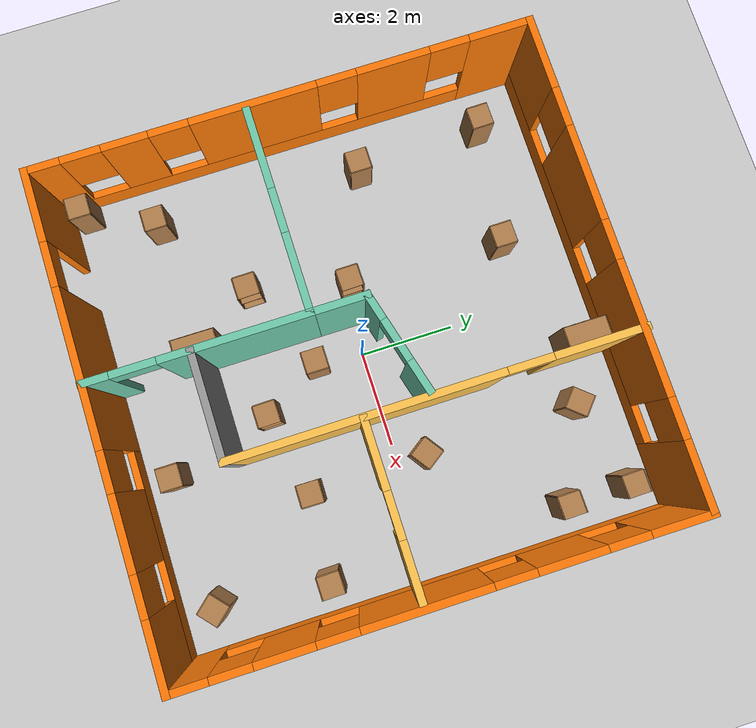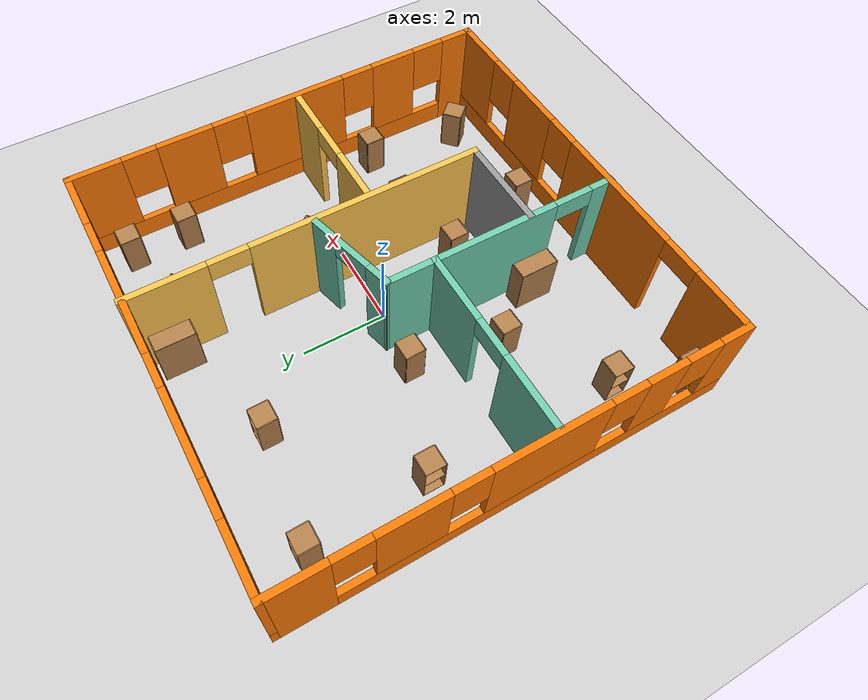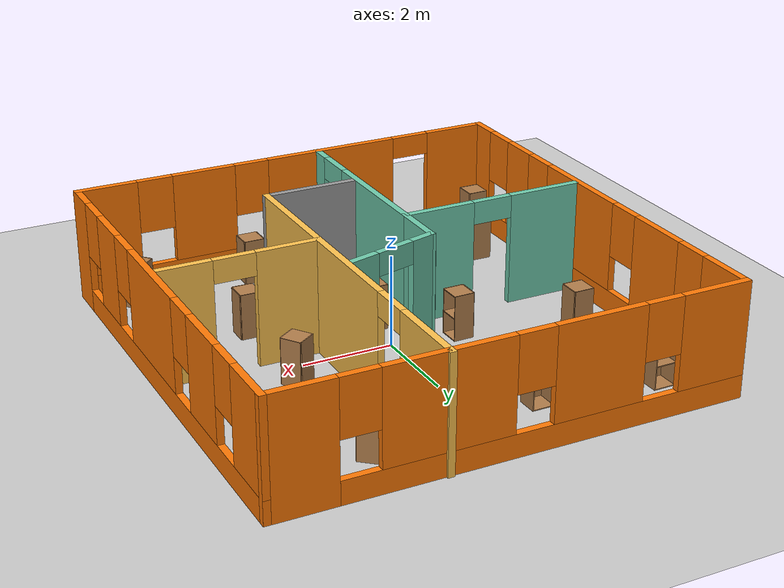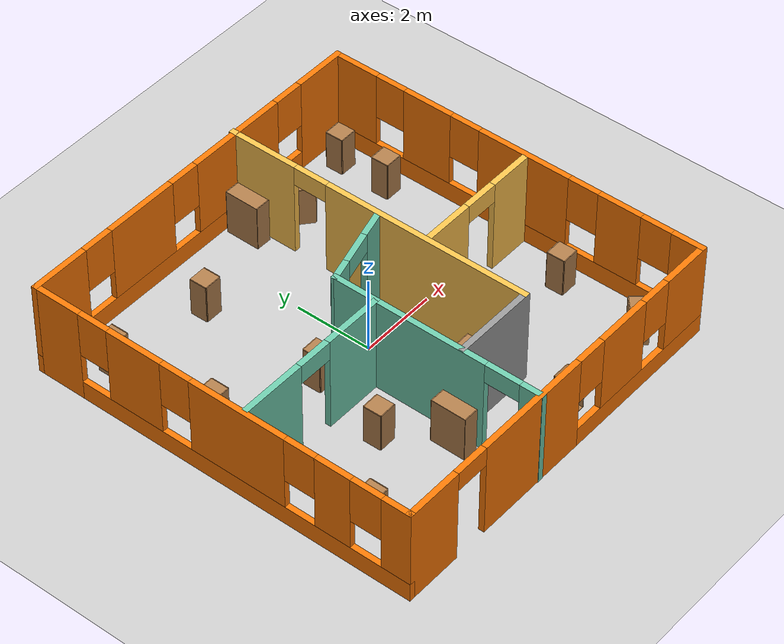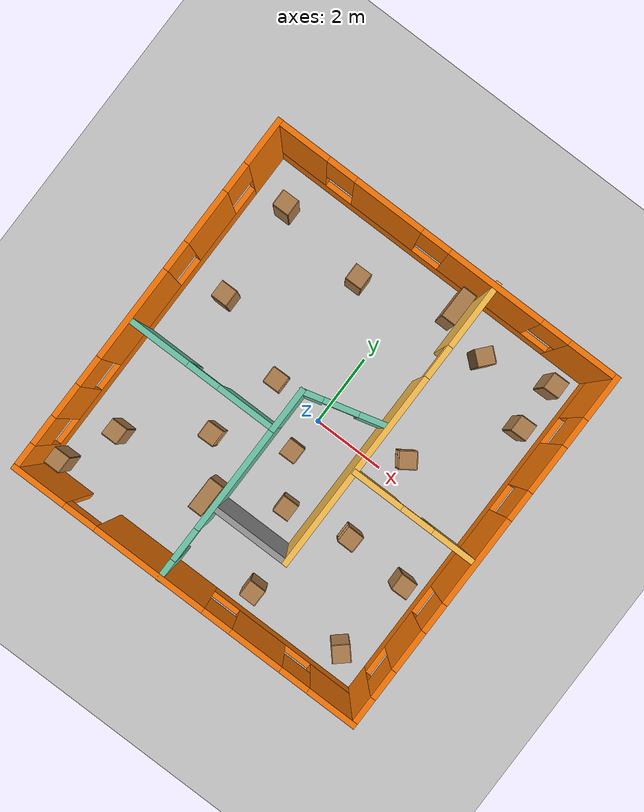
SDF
<sdf version="1.6">
 <world name="default">
  <light name="sun" type="directional">
   <pose>0 0 10 0 -0 0</pose>
   <diffuse>0.8 0.8 0.8 1</diffuse>
   <specular>0.2 0.2 0.2 1</specular>
   <attenuation>
    <range>1000</range>
    <constant>0.9</constant>
    <linear>0.01</linear>
    <quadratic>0.001</quadratic>
   </attenuation>
   <direction>-0.5 0.1 -0.9</direction>
   <spot><inner_angle>0</inner_angle><outer_angle>0</outer_angle><falloff>0</falloff></spot>
  </light>
  <model name="ground_plane">
   <static>1</static>
   <link name="link">
    <collision name="collision">
     <geometry><plane><normal>0 0 1</normal><size>100 100</size></plane></geometry>
     <surface><friction><ode><mu>100</mu><mu2>50</mu2></ode></friction></surface>
    </collision>
    <visual name="visual">
     <cast_shadows>0</cast_shadows>
     <geometry><plane><normal>0 0 1</normal><size>100 100</size></plane></geometry>
     <material>
      <script><uri>file://media/materials/scripts/gazebo.material</uri><name>Gazebo/Grey</name></script>
     </material>
    </visual>
   </link>
  </model>
  <gravity>0 0 -9.8</gravity>
  <magnetic_field>6e-06 2.3e-05 -4.2e-05</magnetic_field>
  <atmosphere type="adiabatic"/>
  <physics type="ode">
   <max_step_size>0.001</max_step_size>
   <real_time_factor>1</real_time_factor>
   <real_time_update_rate>1000</real_time_update_rate>
  </physics>
  <scene><ambient>0.4 0.4 0.4 1</ambient><background>0.7 0.7 0.7 1</background><shadows>1</shadows></scene>
  <spherical_coordinates>
   <surface_model>EARTH_WGS84</surface_model>
   <latitude_deg>0</latitude_deg>
   <longitude_deg>0</longitude_deg>
   <elevation>0</elevation>
   <heading_deg>0</heading_deg>
  </spherical_coordinates>
  <model name="Untitled">
   <pose>-0.0101 -0.055997 0 0 -0 0</pose>
   <link name="Wall_0">
    <pose>-4.925 -0.01837 0 0 -0 -1.5708</pose>
    <visual name="Wall_0_Visual_0">
     <pose>-4.46509 0 1.25 0 -0 0</pose>
     <geometry><box><size>1.31981 0.15 2.5</size></box></geometry>
     <material>
      <script><uri>file://media/materials/scripts/gazebo.material</uri><name>Gazebo/Grey</name></script>
      <ambient>0.996078 0.47451 0.0196078 1</ambient>
     </material>
     <meta><layer>0</layer></meta>
    </visual>
    <collision name="Wall_0_Collision_0">
     <geometry><box><size>1.31981 0.15 2.5</size></box></geometry>
     <pose>-4.46509 0 1.25 0 -0 0</pose>
    </collision>
    <visual name="Wall_0_Visual_1">
     <pose>0.659906 0 0.25 0 -0 0</pose>
     <geometry><box><size>8.93019 0.15 0.5</size></box></geometry>
     <material>
      <script><uri>file://media/materials/scripts/gazebo.material</uri><name>Gazebo/Grey</name></script>
      <ambient>0.996078 0.47451 0.0196078 1</ambient>
     </material>
     <meta><layer>0</layer></meta>
    </visual>
    <collision name="Wall_0_Collision_1">
     <geometry><box><size>8.93019 0.15 0.5</size></box></geometry>
     <pose>0.659906 0 0.25 0 -0 0</pose>
    </collision>
    <visual name="Wall_0_Visual_2">
     <pose>-2.26138 0 1.5 0 -0 0</pose>
     <geometry><box><size>1.48762 0.15 2</size></box></geometry>
     <material>
      <script><uri>file://media/materials/scripts/gazebo.material</uri><name>Gazebo/Grey</name></script>
      <ambient>0.996078 0.47451 0.0196078 1</ambient>
     </material>
     <meta><layer>0</layer></meta>
    </visual>
    <collision name="Wall_0_Collision_2">
     <geometry><box><size>1.48762 0.15 2</size></box></geometry>
     <pose>-2.26138 0 1.5 0 -0 0</pose>
    </collision>
    <visual name="Wall_0_Visual_3">
     <pose>0.558242 0 1.5 0 -0 0</pose>
     <geometry><box><size>2.55163 0.15 2</size></box></geometry>
     <material>
      <script><uri>file://media/materials/scripts/gazebo.material</uri><name>Gazebo/Grey</name></script>
      <ambient>0.996078 0.47451 0.0196078 1</ambient>
     </material>
     <meta><layer>0</layer></meta>
    </visual>
    <collision name="Wall_0_Collision_3">
     <geometry><box><size>2.55163 0.15 2</size></box></geometry>
     <pose>0.558242 0 1.5 0 -0 0</pose>
    </collision>
    <visual name="Wall_0_Visual_4">
     <pose>3.09856 0 1.5 0 -0 0</pose>
     <geometry><box><size>0.929013 0.15 2</size></box></geometry>
     <material>
      <script><uri>file://media/materials/scripts/gazebo.material</uri><name>Gazebo/Grey</name></script>
      <ambient>0.996078 0.47451 0.0196078 1</ambient>
     </material>
     <meta><layer>0</layer></meta>
    </visual>
    <collision name="Wall_0_Collision_4">
     <geometry><box><size>0.929013 0.15 2</size></box></geometry>
     <pose>3.09856 0 1.5 0 -0 0</pose>
    </collision>
    <visual name="Wall_0_Visual_5">
     <pose>4.74403 0 1.5 0 -0 0</pose>
     <geometry><box><size>0.761933 0.15 2</size></box></geometry>
     <material>
      <script><uri>file://media/materials/scripts/gazebo.material</uri><name>Gazebo/Grey</name></script>
      <ambient>0.996078 0.47451 0.0196078 1</ambient>
     </material>
     <meta><layer>0</layer></meta>
    </visual>
    <collision name="Wall_0_Collision_5">
     <geometry><box><size>0.761933 0.15 2</size></box></geometry>
     <pose>4.74403 0 1.5 0 -0 0</pose>
    </collision>
    <visual name="Wall_0_Visual_6">
     <pose>-3.40519 0 1.9 0 -0 0</pose>
     <geometry><box><size>0.8 0.15 1.2</size></box></geometry>
     <material>
      <script><uri>file://media/materials/scripts/gazebo.material</uri><name>Gazebo/Grey</name></script>
      <ambient>0.996078 0.47451 0.0196078 1</ambient>
     </material>
     <meta><layer>0</layer></meta>
    </visual>
    <collision name="Wall_0_Collision_6">
     <geometry><box><size>0.8 0.15 1.2</size></box></geometry>
     <pose>-3.40519 0 1.9 0 -0 0</pose>
    </collision>
    <visual name="Wall_0_Visual_7">
     <pose>-1.11757 0 1.9 0 -0 0</pose>
     <geometry><box><size>0.8 0.15 1.2</size></box></geometry>
     <material>
      <script><uri>file://media/materials/scripts/gazebo.material</uri><name>Gazebo/Grey</name></script>
      <ambient>0.996078 0.47451 0.0196078 1</ambient>
     </material>
     <meta><layer>0</layer></meta>
    </visual>
    <collision name="Wall_0_Collision_7">
     <geometry><box><size>0.8 0.15 1.2</size></box></geometry>
     <pose>-1.11757 0 1.9 0 -0 0</pose>
    </collision>
    <visual name="Wall_0_Visual_8">
     <pose>2.23405 0 1.9 0 -0 0</pose>
     <geometry><box><size>0.8 0.15 1.2</size></box></geometry>
     <material>
      <script><uri>file://media/materials/scripts/gazebo.material</uri><name>Gazebo/Grey</name></script>
      <ambient>0.996078 0.47451 0.0196078 1</ambient>
     </material>
     <meta><layer>0</layer></meta>
    </visual>
    <collision name="Wall_0_Collision_8">
     <geometry><box><size>0.8 0.15 1.2</size></box></geometry>
     <pose>2.23405 0 1.9 0 -0 0</pose>
    </collision>
    <visual name="Wall_0_Visual_9">
     <pose>3.96307 0 1.9 0 -0 0</pose>
     <geometry><box><size>0.8 0.15 1.2</size></box></geometry>
     <material>
      <script><uri>file://media/materials/scripts/gazebo.material</uri><name>Gazebo/Grey</name></script>
      <ambient>0.996078 0.47451 0.0196078 1</ambient>
     </material>
     <meta><layer>0</layer></meta>
    </visual>
    <collision name="Wall_0_Collision_9">
     <geometry><box><size>0.8 0.15 1.2</size></box></geometry>
     <pose>3.96307 0 1.9 0 -0 0</pose>
    </collision>
   </link>
   <link name="Wall_1">
    <pose>0 -5.06837 0 0 -0 0</pose>
    <visual name="Wall_1_Visual_0">
     <pose>-4.24602 0 1.25 0 -0 0</pose>
     <geometry><box><size>1.50797 0.15 2.5</size></box></geometry>
     <material>
      <script><uri>file://media/materials/scripts/gazebo.material</uri><name>Gazebo/Grey</name></script>
      <ambient>0.996078 0.47451 0.0196078 1</ambient>
     </material>
     <meta><layer>0</layer></meta>
    </visual>
    <collision name="Wall_1_Collision_0">
     <geometry><box><size>1.50797 0.15 2.5</size></box></geometry>
     <pose>-4.24602 0 1.25 0 -0 0</pose>
    </collision>
    <visual name="Wall_1_Visual_1">
     <pose>-1.02202 0 1.25 0 -0 0</pose>
     <geometry><box><size>3.14003 0.15 2.5</size></box></geometry>
     <material>
      <script><uri>file://media/materials/scripts/gazebo.material</uri><name>Gazebo/Grey</name></script>
      <ambient>0.996078 0.47451 0.0196078 1</ambient>
     </material>
     <meta><layer>0</layer></meta>
    </visual>
    <collision name="Wall_1_Collision_1">
     <geometry><box><size>3.14003 0.15 2.5</size></box></geometry>
     <pose>-1.02202 0 1.25 0 -0 0</pose>
    </collision>
    <visual name="Wall_1_Visual_2">
     <pose>2.774 0 0.25 0 -0 0</pose>
     <geometry><box><size>4.452 0.15 0.5</size></box></geometry>
     <material>
      <script><uri>file://media/materials/scripts/gazebo.material</uri><name>Gazebo/Grey</name></script>
      <ambient>0.996078 0.47451 0.0196078 1</ambient>
     </material>
     <meta><layer>0</layer></meta>
    </visual>
    <collision name="Wall_1_Collision_2">
     <geometry><box><size>4.452 0.15 0.5</size></box></geometry>
     <pose>2.774 0 0.25 0 -0 0</pose>
    </collision>
    <visual name="Wall_1_Visual_3">
     <pose>2.07851 0 1.5 0 -0 0</pose>
     <geometry><box><size>1.46102 0.15 2</size></box></geometry>
     <material>
      <script><uri>file://media/materials/scripts/gazebo.material</uri><name>Gazebo/Grey</name></script>
      <ambient>0.996078 0.47451 0.0196078 1</ambient>
     </material>
     <meta><layer>0</layer></meta>
    </visual>
    <collision name="Wall_1_Collision_3">
     <geometry><box><size>1.46102 0.15 2</size></box></geometry>
     <pose>2.07851 0 1.5 0 -0 0</pose>
    </collision>
    <visual name="Wall_1_Visual_4">
     <pose>4.30451 0 1.5 0 -0 0</pose>
     <geometry><box><size>1.39099 0.15 2</size></box></geometry>
     <material>
      <script><uri>file://media/materials/scripts/gazebo.material</uri><name>Gazebo/Grey</name></script>
      <ambient>0.996078 0.47451 0.0196078 1</ambient>
     </material>
     <meta><layer>0</layer></meta>
    </visual>
    <collision name="Wall_1_Collision_4">
     <geometry><box><size>1.39099 0.15 2</size></box></geometry>
     <pose>4.30451 0 1.5 0 -0 0</pose>
    </collision>
    <visual name="Wall_1_Visual_5">
     <pose>0.947997 0 1.9 0 -0 0</pose>
     <geometry><box><size>0.8 0.15 1.2</size></box></geometry>
     <material>
      <script><uri>file://media/materials/scripts/gazebo.material</uri><name>Gazebo/Grey</name></script>
      <ambient>0.996078 0.47451 0.0196078 1</ambient>
     </material>
     <meta><layer>0</layer></meta>
    </visual>
    <collision name="Wall_1_Collision_5">
     <geometry><box><size>0.8 0.15 1.2</size></box></geometry>
     <pose>0.947997 0 1.9 0 -0 0</pose>
    </collision>
    <visual name="Wall_1_Visual_6">
     <pose>3.20901 0 1.9 0 -0 0</pose>
     <geometry><box><size>0.8 0.15 1.2</size></box></geometry>
     <material>
      <script><uri>file://media/materials/scripts/gazebo.material</uri><name>Gazebo/Grey</name></script>
      <ambient>0.996078 0.47451 0.0196078 1</ambient>
     </material>
     <meta><layer>0</layer></meta>
    </visual>
    <collision name="Wall_1_Collision_6">
     <geometry><box><size>0.8 0.15 1.2</size></box></geometry>
     <pose>3.20901 0 1.9 0 -0 0</pose>
    </collision>
    <visual name="Wall_1_Visual_7">
     <pose>-3.04203 0 2.25 0 -0 0</pose>
     <geometry><box><size>0.9 0.15 0.5</size></box></geometry>
     <material>
      <script><uri>file://media/materials/scripts/gazebo.material</uri><name>Gazebo/Grey</name></script>
      <ambient>0.996078 0.47451 0.0196078 1</ambient>
     </material>
     <meta><layer>0</layer></meta>
    </visual>
    <collision name="Wall_1_Collision_7">
     <geometry><box><size>0.9 0.15 0.5</size></box></geometry>
     <pose>-3.04203 0 2.25 0 -0 0</pose>
    </collision>
   </link>
   <link name="Wall_11">
    <pose>3.11224 -0.381007 0 0 -0 0</pose>
    <visual name="Wall_11_Visual_0">
     <pose>-1.03831 0 1.25 0 -0 0</pose>
     <geometry><box><size>1.42338 0.15 2.5</size></box></geometry>
     <material>
      <script><uri>file://media/materials/scripts/gazebo.material</uri><name>Gazebo/Grey</name></script>
      <ambient>1 0.764706 0.305882 1</ambient>
     </material>
     <meta><layer>0</layer></meta>
    </visual>
    <collision name="Wall_11_Collision_0">
     <geometry><box><size>1.42338 0.15 2.5</size></box></geometry>
     <pose>-1.03831 0 1.25 0 -0 0</pose>
    </collision>
    <visual name="Wall_11_Visual_1">
     <pose>1.16169 0 1.25 0 -0 0</pose>
     <geometry><box><size>1.17662 0.15 2.5</size></box></geometry>
     <material>
      <script><uri>file://media/materials/scripts/gazebo.material</uri><name>Gazebo/Grey</name></script>
      <ambient>1 0.764706 0.305882 1</ambient>
     </material>
     <meta><layer>0</layer></meta>
    </visual>
    <collision name="Wall_11_Collision_1">
     <geometry><box><size>1.17662 0.15 2.5</size></box></geometry>
     <pose>1.16169 0 1.25 0 -0 0</pose>
    </collision>
    <visual name="Wall_11_Visual_2">
     <pose>0.123376 0 2.25 0 -0 0</pose>
     <geometry><box><size>0.9 0.15 0.5</size></box></geometry>
     <material>
      <script><uri>file://media/materials/scripts/gazebo.material</uri><name>Gazebo/Grey</name></script>
      <ambient>1 0.764706 0.305882 1</ambient>
     </material>
     <meta><layer>0</layer></meta>
    </visual>
    <collision name="Wall_11_Collision_2">
     <geometry><box><size>0.9 0.15 0.5</size></box></geometry>
     <pose>0.123376 0 2.25 0 -0 0</pose>
    </collision>
   </link>
   <link name="Wall_13">
    <collision name="Wall_13_Collision">
     <geometry><box><size>1.25 0.15 2.5</size></box></geometry>
     <pose>0 0 1.25 0 -0 0</pose>
    </collision>
    <visual name="Wall_13_Visual">
     <pose>0 0 1.25 0 -0 0</pose>
     <geometry><box><size>1.25 0.15 2.5</size></box></geometry>
     <material>
      <script><uri>file://media/materials/scripts/gazebo.material</uri><name>Gazebo/Grey</name></script>
      <ambient>0.435294 0.796078 0.67451 1</ambient>
     </material>
     <meta><layer>0</layer></meta>
    </visual>
    <pose>-0.709347 -0.177891 0 0 -0 1.5708</pose>
   </link>
   <link name="Wall_14">
    <pose>0.304875 0.643869 0 0 -0 0.261799</pose>
    <visual name="Wall_14_Visual_0">
     <pose>-0.816473 0 1.25 0 -0 0</pose>
     <geometry><box><size>0.617054 0.15 2.5</size></box></geometry>
     <material>
      <script><uri>file://media/materials/scripts/gazebo.material</uri><name>Gazebo/Grey</name></script>
      <ambient>0.435294 0.796078 0.67451 1</ambient>
     </material>
     <meta><layer>0</layer></meta>
    </visual>
    <collision name="Wall_14_Collision_0">
     <geometry><box><size>0.617054 0.15 2.5</size></box></geometry>
     <pose>-0.816473 0 1.25 0 -0 0</pose>
    </collision>
    <visual name="Wall_14_Visual_1">
     <pose>0.758527 0 1.25 0 -0 0</pose>
     <geometry><box><size>0.732946 0.15 2.5</size></box></geometry>
     <material>
      <script><uri>file://media/materials/scripts/gazebo.material</uri><name>Gazebo/Grey</name></script>
      <ambient>0.435294 0.796078 0.67451 1</ambient>
     </material>
     <meta><layer>0</layer></meta>
    </visual>
    <collision name="Wall_14_Collision_1">
     <geometry><box><size>0.732946 0.15 2.5</size></box></geometry>
     <pose>0.758527 0 1.25 0 -0 0</pose>
    </collision>
    <visual name="Wall_14_Visual_2">
     <pose>-0.057946 0 2.25 0 -0 0</pose>
     <geometry><box><size>0.9 0.15 0.5</size></box></geometry>
     <material>
      <script><uri>file://media/materials/scripts/gazebo.material</uri><name>Gazebo/Grey</name></script>
      <ambient>0.435294 0.796078 0.67451 1</ambient>
     </material>
     <meta><layer>0</layer></meta>
    </visual>
    <collision name="Wall_14_Collision_2">
     <geometry><box><size>0.9 0.15 0.5</size></box></geometry>
     <pose>-0.057946 0 2.25 0 -0 0</pose>
    </collision>
   </link>
   <link name="Wall_2">
    <pose>4.925 -0.01837 0 0 -0 1.5708</pose>
    <visual name="Wall_2_Visual_0">
     <pose>-4.70413 0 1.25 0 -0 0</pose>
     <geometry><box><size>0.841734 0.15 2.5</size></box></geometry>
     <material>
      <script><uri>file://media/materials/scripts/gazebo.material</uri><name>Gazebo/Grey</name></script>
      <ambient>0.996078 0.47451 0.0196078 1</ambient>
     </material>
     <meta><layer>0</layer></meta>
    </visual>
    <collision name="Wall_2_Collision_0">
     <geometry><box><size>0.841734 0.15 2.5</size></box></geometry>
     <pose>-4.70413 0 1.25 0 -0 0</pose>
    </collision>
    <visual name="Wall_2_Visual_1">
     <pose>0.420867 0 0.25 0 -0 0</pose>
     <geometry><box><size>9.40827 0.15 0.5</size></box></geometry>
     <material>
      <script><uri>file://media/materials/scripts/gazebo.material</uri><name>Gazebo/Grey</name></script>
      <ambient>0.996078 0.47451 0.0196078 1</ambient>
     </material>
     <meta><layer>0</layer></meta>
    </visual>
    <collision name="Wall_2_Collision_1">
     <geometry><box><size>9.40827 0.15 0.5</size></box></geometry>
     <pose>0.420867 0 0.25 0 -0 0</pose>
    </collision>
    <visual name="Wall_2_Visual_2">
     <pose>-2.91236 0 1.5 0 -0 0</pose>
     <geometry><box><size>1.14181 0.15 2</size></box></geometry>
     <material>
      <script><uri>file://media/materials/scripts/gazebo.material</uri><name>Gazebo/Grey</name></script>
      <ambient>0.996078 0.47451 0.0196078 1</ambient>
     </material>
     <meta><layer>0</layer></meta>
    </visual>
    <collision name="Wall_2_Collision_2">
     <geometry><box><size>1.14181 0.15 2</size></box></geometry>
     <pose>-2.91236 0 1.5 0 -0 0</pose>
    </collision>
    <visual name="Wall_2_Visual_3">
     <pose>-0.30554 0 1.5 0 -0 0</pose>
     <geometry><box><size>2.47182 0.15 2</size></box></geometry>
     <material>
      <script><uri>file://media/materials/scripts/gazebo.material</uri><name>Gazebo/Grey</name></script>
      <ambient>0.996078 0.47451 0.0196078 1</ambient>
     </material>
     <meta><layer>0</layer></meta>
    </visual>
    <collision name="Wall_2_Collision_3">
     <geometry><box><size>2.47182 0.15 2</size></box></geometry>
     <pose>-0.30554 0 1.5 0 -0 0</pose>
    </collision>
    <visual name="Wall_2_Visual_4">
     <pose>2.39438 0 1.5 0 -0 0</pose>
     <geometry><box><size>1.32802 0.15 2</size></box></geometry>
     <material>
      <script><uri>file://media/materials/scripts/gazebo.material</uri><name>Gazebo/Grey</name></script>
      <ambient>0.996078 0.47451 0.0196078 1</ambient>
     </material>
     <meta><layer>0</layer></meta>
    </visual>
    <collision name="Wall_2_Collision_4">
     <geometry><box><size>1.32802 0.15 2</size></box></geometry>
     <pose>2.39438 0 1.5 0 -0 0</pose>
    </collision>
    <visual name="Wall_2_Visual_5">
     <pose>4.49169 0 1.5 0 -0 0</pose>
     <geometry><box><size>1.26661 0.15 2</size></box></geometry>
     <material>
      <script><uri>file://media/materials/scripts/gazebo.material</uri><name>Gazebo/Grey</name></script>
      <ambient>0.996078 0.47451 0.0196078 1</ambient>
     </material>
     <meta><layer>0</layer></meta>
    </visual>
    <collision name="Wall_2_Collision_5">
     <geometry><box><size>1.26661 0.15 2</size></box></geometry>
     <pose>4.49169 0 1.5 0 -0 0</pose>
    </collision>
    <visual name="Wall_2_Visual_6">
     <pose>-3.88327 0 1.9 0 -0 0</pose>
     <geometry><box><size>0.8 0.15 1.2</size></box></geometry>
     <material>
      <script><uri>file://media/materials/scripts/gazebo.material</uri><name>Gazebo/Grey</name></script>
      <ambient>0.996078 0.47451 0.0196078 1</ambient>
     </material>
     <meta><layer>0</layer></meta>
    </visual>
    <collision name="Wall_2_Collision_6">
     <geometry><box><size>0.8 0.15 1.2</size></box></geometry>
     <pose>-3.88327 0 1.9 0 -0 0</pose>
    </collision>
    <visual name="Wall_2_Visual_7">
     <pose>-1.94145 0 1.9 0 -0 0</pose>
     <geometry><box><size>0.8 0.15 1.2</size></box></geometry>
     <material>
      <script><uri>file://media/materials/scripts/gazebo.material</uri><name>Gazebo/Grey</name></script>
      <ambient>0.996078 0.47451 0.0196078 1</ambient>
     </material>
     <meta><layer>0</layer></meta>
    </visual>
    <collision name="Wall_2_Collision_7">
     <geometry><box><size>0.8 0.15 1.2</size></box></geometry>
     <pose>-1.94145 0 1.9 0 -0 0</pose>
    </collision>
    <visual name="Wall_2_Visual_8">
     <pose>1.33037 0 1.9 0 -0 0</pose>
     <geometry><box><size>0.8 0.15 1.2</size></box></geometry>
     <material>
      <script><uri>file://media/materials/scripts/gazebo.material</uri><name>Gazebo/Grey</name></script>
      <ambient>0.996078 0.47451 0.0196078 1</ambient>
     </material>
     <meta><layer>0</layer></meta>
    </visual>
    <collision name="Wall_2_Collision_8">
     <geometry><box><size>0.8 0.15 1.2</size></box></geometry>
     <pose>1.33037 0 1.9 0 -0 0</pose>
    </collision>
    <visual name="Wall_2_Visual_9">
     <pose>3.45839 0 1.9 0 -0 0</pose>
     <geometry><box><size>0.8 0.15 1.2</size></box></geometry>
     <material>
      <script><uri>file://media/materials/scripts/gazebo.material</uri><name>Gazebo/Grey</name></script>
      <ambient>0.996078 0.47451 0.0196078 1</ambient>
     </material>
     <meta><layer>0</layer></meta>
    </visual>
    <collision name="Wall_2_Collision_9">
     <geometry><box><size>0.8 0.15 1.2</size></box></geometry>
     <pose>3.45839 0 1.9 0 -0 0</pose>
    </collision>
   </link>
   <link name="Wall_3">
    <pose>0 5.03163 0 0 -0 3.14159</pose>
    <visual name="Wall_3_Visual_0">
     <pose>-4.27791 0 1.25 0 -0 0</pose>
     <geometry><box><size>1.44419 0.15 2.5</size></box></geometry>
     <material>
      <script><uri>file://media/materials/scripts/gazebo.material</uri><name>Gazebo/Grey</name></script>
      <ambient>0.996078 0.47451 0.0196078 1</ambient>
     </material>
     <meta><layer>0</layer></meta>
    </visual>
    <collision name="Wall_3_Collision_0">
     <geometry><box><size>1.44419 0.15 2.5</size></box></geometry>
     <pose>-4.27791 0 1.25 0 -0 0</pose>
    </collision>
    <visual name="Wall_3_Visual_1">
     <pose>0.722093 0 0.25 0 -0 0</pose>
     <geometry><box><size>8.55581 0.15 0.5</size></box></geometry>
     <material>
      <script><uri>file://media/materials/scripts/gazebo.material</uri><name>Gazebo/Grey</name></script>
      <ambient>0.996078 0.47451 0.0196078 1</ambient>
     </material>
     <meta><layer>0</layer></meta>
    </visual>
    <collision name="Wall_3_Collision_1">
     <geometry><box><size>8.55581 0.15 0.5</size></box></geometry>
     <pose>0.722093 0 0.25 0 -0 0</pose>
    </collision>
    <visual name="Wall_3_Visual_2">
     <pose>-1.4135 0 1.5 0 -0 0</pose>
     <geometry><box><size>2.68463 0.15 2</size></box></geometry>
     <material>
      <script><uri>file://media/materials/scripts/gazebo.material</uri><name>Gazebo/Grey</name></script>
      <ambient>0.996078 0.47451 0.0196078 1</ambient>
     </material>
     <meta><layer>0</layer></meta>
    </visual>
    <collision name="Wall_3_Collision_2">
     <geometry><box><size>2.68463 0.15 2</size></box></geometry>
     <pose>-1.4135 0 1.5 0 -0 0</pose>
    </collision>
    <visual name="Wall_3_Visual_3">
     <pose>1.69872 0 1.5 0 -0 0</pose>
     <geometry><box><size>1.93982 0.15 2</size></box></geometry>
     <material>
      <script><uri>file://media/materials/scripts/gazebo.material</uri><name>Gazebo/Grey</name></script>
      <ambient>0.996078 0.47451 0.0196078 1</ambient>
     </material>
     <meta><layer>0</layer></meta>
    </visual>
    <collision name="Wall_3_Collision_3">
     <geometry><box><size>1.93982 0.15 2</size></box></geometry>
     <pose>1.69872 0 1.5 0 -0 0</pose>
    </collision>
    <visual name="Wall_3_Visual_4">
     <pose>4.23432 0 1.5 0 -0 0</pose>
     <geometry><box><size>1.53137 0.15 2</size></box></geometry>
     <material>
      <script><uri>file://media/materials/scripts/gazebo.material</uri><name>Gazebo/Grey</name></script>
      <ambient>0.996078 0.47451 0.0196078 1</ambient>
     </material>
     <meta><layer>0</layer></meta>
    </visual>
    <collision name="Wall_3_Collision_4">
     <geometry><box><size>1.53137 0.15 2</size></box></geometry>
     <pose>4.23432 0 1.5 0 -0 0</pose>
    </collision>
    <visual name="Wall_3_Visual_5">
     <pose>-3.15581 0 1.9 0 -0 0</pose>
     <geometry><box><size>0.8 0.15 1.2</size></box></geometry>
     <material>
      <script><uri>file://media/materials/scripts/gazebo.material</uri><name>Gazebo/Grey</name></script>
      <ambient>0.996078 0.47451 0.0196078 1</ambient>
     </material>
     <meta><layer>0</layer></meta>
    </visual>
    <collision name="Wall_3_Collision_5">
     <geometry><box><size>0.8 0.15 1.2</size></box></geometry>
     <pose>-3.15581 0 1.9 0 -0 0</pose>
    </collision>
    <visual name="Wall_3_Visual_6">
     <pose>0.328812 0 1.9 0 -0 0</pose>
     <geometry><box><size>0.8 0.15 1.2</size></box></geometry>
     <material>
      <script><uri>file://media/materials/scripts/gazebo.material</uri><name>Gazebo/Grey</name></script>
      <ambient>0.996078 0.47451 0.0196078 1</ambient>
     </material>
     <meta><layer>0</layer></meta>
    </visual>
    <collision name="Wall_3_Collision_6">
     <geometry><box><size>0.8 0.15 1.2</size></box></geometry>
     <pose>0.328812 0 1.9 0 -0 0</pose>
    </collision>
    <visual name="Wall_3_Visual_7">
     <pose>3.06863 0 1.9 0 -0 0</pose>
     <geometry><box><size>0.8 0.15 1.2</size></box></geometry>
     <material>
      <script><uri>file://media/materials/scripts/gazebo.material</uri><name>Gazebo/Grey</name></script>
      <ambient>0.996078 0.47451 0.0196078 1</ambient>
     </material>
     <meta><layer>0</layer></meta>
    </visual>
    <collision name="Wall_3_Collision_7">
     <geometry><box><size>0.8 0.15 1.2</size></box></geometry>
     <pose>3.06863 0 1.9 0 -0 0</pose>
    </collision>
   </link>
   <link name="Wall_5">
    <pose>-2.75935 -0.727891 0 0 -0 0</pose>
    <visual name="Wall_5_Visual_0">
     <pose>-1.28254 0 1.25 0 -0 0</pose>
     <geometry><box><size>1.68492 0.15 2.5</size></box></geometry>
     <material>
      <script><uri>file://media/materials/scripts/gazebo.material</uri><name>Gazebo/Grey</name></script>
      <ambient>0.435294 0.796078 0.67451 1</ambient>
     </material>
     <meta><layer>0</layer></meta>
    </visual>
    <collision name="Wall_5_Collision_0">
     <geometry><box><size>1.68492 0.15 2.5</size></box></geometry>
     <pose>-1.28254 0 1.25 0 -0 0</pose>
    </collision>
    <visual name="Wall_5_Visual_1">
     <pose>1.29246 0 1.25 0 -0 0</pose>
     <geometry><box><size>1.66508 0.15 2.5</size></box></geometry>
     <material>
      <script><uri>file://media/materials/scripts/gazebo.material</uri><name>Gazebo/Grey</name></script>
      <ambient>0.435294 0.796078 0.67451 1</ambient>
     </material>
     <meta><layer>0</layer></meta>
    </visual>
    <collision name="Wall_5_Collision_1">
     <geometry><box><size>1.66508 0.15 2.5</size></box></geometry>
     <pose>1.29246 0 1.25 0 -0 0</pose>
    </collision>
    <visual name="Wall_5_Visual_2">
     <pose>0.009916 0 2.25 0 -0 0</pose>
     <geometry><box><size>0.9 0.15 0.5</size></box></geometry>
     <material>
      <script><uri>file://media/materials/scripts/gazebo.material</uri><name>Gazebo/Grey</name></script>
      <ambient>0.435294 0.796078 0.67451 1</ambient>
     </material>
     <meta><layer>0</layer></meta>
    </visual>
    <collision name="Wall_5_Collision_2">
     <geometry><box><size>0.9 0.15 0.5</size></box></geometry>
     <pose>0.009916 0 2.25 0 -0 0</pose>
    </collision>
   </link>
   <link name="Wall_6">
    <pose>-0.709347 -2.90289 0 0 -0 -1.5708</pose>
    <visual name="Wall_6_Visual_0">
     <pose>-0.744227 0 1.25 0 -0 0</pose>
     <geometry><box><size>3.01155 0.15 2.5</size></box></geometry>
     <material>
      <script><uri>file://media/materials/scripts/gazebo.material</uri><name>Gazebo/Grey</name></script>
      <ambient>0.435294 0.796078 0.67451 1</ambient>
     </material>
     <meta><layer>0</layer></meta>
    </visual>
    <collision name="Wall_6_Collision_0">
     <geometry><box><size>3.01155 0.15 2.5</size></box></geometry>
     <pose>-0.744227 0 1.25 0 -0 0</pose>
    </collision>
    <visual name="Wall_6_Visual_1">
     <pose>1.95577 0 1.25 0 -0 0</pose>
     <geometry><box><size>0.588453 0.15 2.5</size></box></geometry>
     <material>
      <script><uri>file://media/materials/scripts/gazebo.material</uri><name>Gazebo/Grey</name></script>
      <ambient>0.435294 0.796078 0.67451 1</ambient>
     </material>
     <meta><layer>0</layer></meta>
    </visual>
    <collision name="Wall_6_Collision_1">
     <geometry><box><size>0.588453 0.15 2.5</size></box></geometry>
     <pose>1.95577 0 1.25 0 -0 0</pose>
    </collision>
    <visual name="Wall_6_Visual_2">
     <pose>1.21155 0 2.25 0 -0 0</pose>
     <geometry><box><size>0.9 0.15 0.5</size></box></geometry>
     <material>
      <script><uri>file://media/materials/scripts/gazebo.material</uri><name>Gazebo/Grey</name></script>
      <ambient>0.435294 0.796078 0.67451 1</ambient>
     </material>
     <meta><layer>0</layer></meta>
    </visual>
    <collision name="Wall_6_Collision_2">
     <geometry><box><size>0.9 0.15 0.5</size></box></geometry>
     <pose>1.21155 0 2.25 0 -0 0</pose>
    </collision>
   </link>
   <link name="Wall_8">
    <pose>1.41279 1.02789 0 0 -0 -1.5708</pose>
    <visual name="Wall_8_Visual_0">
     <pose>-3.18766 0 1.25 0 -0 0</pose>
     <geometry><box><size>1.87468 0.15 2.5</size></box></geometry>
     <material>
      <script><uri>file://media/materials/scripts/gazebo.material</uri><name>Gazebo/Grey</name></script>
      <ambient>1 0.764706 0.305882 1</ambient>
     </material>
     <meta><layer>0</layer></meta>
    </visual>
    <collision name="Wall_8_Collision_0">
     <geometry><box><size>1.87468 0.15 2.5</size></box></geometry>
     <pose>-3.18766 0 1.25 0 -0 0</pose>
    </collision>
    <visual name="Wall_8_Visual_1">
     <pose>1.38734 0 1.25 0 -0 0</pose>
     <geometry><box><size>5.47532 0.15 2.5</size></box></geometry>
     <material>
      <script><uri>file://media/materials/scripts/gazebo.material</uri><name>Gazebo/Grey</name></script>
      <ambient>1 0.764706 0.305882 1</ambient>
     </material>
     <meta><layer>0</layer></meta>
    </visual>
    <collision name="Wall_8_Collision_1">
     <geometry><box><size>5.47532 0.15 2.5</size></box></geometry>
     <pose>1.38734 0 1.25 0 -0 0</pose>
    </collision>
    <visual name="Wall_8_Visual_2">
     <pose>-1.80032 0 2.25 0 -0 0</pose>
     <geometry><box><size>0.9 0.15 0.5</size></box></geometry>
     <material>
      <script><uri>file://media/materials/scripts/gazebo.material</uri><name>Gazebo/Grey</name></script>
      <ambient>1 0.764706 0.305882 1</ambient>
     </material>
     <meta><layer>0</layer></meta>
    </visual>
    <collision name="Wall_8_Collision_2">
     <geometry><box><size>0.9 0.15 0.5</size></box></geometry>
     <pose>-1.80032 0 2.25 0 -0 0</pose>
    </collision>
   </link>
   <link name="Wall_9">
    <collision name="Wall_9_Collision">
     <geometry><box><size>2.25 0.15 2.5</size></box></geometry>
     <pose>0 0 1.25 0 -0 0</pose>
    </collision>
    <visual name="Wall_9_Visual">
     <pose>0 0 1.25 0 -0 0</pose>
     <geometry><box><size>2.25 0.15 2.5</size></box></geometry>
     <material>
      <script><uri>file://media/materials/scripts/gazebo.material</uri><name>Gazebo/Grey</name></script>
      <ambient>1 1 1 1</ambient>
     </material>
     <meta><layer>0</layer></meta>
    </visual>
    <pose>0.362787 -3.02211 0 0 -0 3.14159</pose>
   </link>
   <static>1</static>
  </model>
  <model name="cabinet">
   <static>1</static>
   <link name="cabinet_bottom_plate">
    <inertial>
     <pose>0 0 -1 0 -0 0</pose>
     <inertia><ixx>2.05</ixx><ixy>0</ixy><ixz>0</ixz><iyy>2.05</iyy><iyz>0</iyz><izz>2.05</izz></inertia>
     <mass>25</mass>
    </inertial>
    <collision name="cabinet_bottom_plate_geom">
     <pose>0 0 0.01 0 -0 0</pose>
     <geometry><box><size>0.45 0.45 0.02</size></box></geometry>
    </collision>
    <visual name="cabinet_bottom_plate_geom_visual">
     <pose>0 0 0.01 0 -0 0</pose>
     <geometry><box><size>0.45 0.45 0.02</size></box></geometry>
     <material>
      <script><uri>file://media/materials/scripts/gazebo.material</uri><name>Gazebo/Wood</name></script>
     </material>
    </visual>
    <collision name="cabinet_bottom_plate_geom_cabinet_back_plate">
     <pose>0.235 0 0.51 0 -0 0</pose>
     <geometry><box><size>0.02 0.45 1.02</size></box></geometry>
    </collision>
    <visual name="cabinet_bottom_plate_geom_cabinet_back_plate_visual">
     <pose>0.235 0 0.51 0 -0 0</pose>
     <geometry><box><size>0.02 0.45 1.02</size></box></geometry>
     <material>
      <script><uri>file://media/materials/scripts/gazebo.material</uri><name>Gazebo/Wood</name></script>
     </material>
    </visual>
    <collision name="cabinet_bottom_plate_geom_cabinet_left_plate">
     <pose>0 0.235 0.51 0 -0 0</pose>
     <geometry><box><size>0.45 0.02 1.02</size></box></geometry>
    </collision>
    <visual name="cabinet_bottom_plate_geom_cabinet_left_plate_visual">
     <pose>0 0.235 0.51 0 -0 0</pose>
     <geometry><box><size>0.45 0.02 1.02</size></box></geometry>
     <material>
      <script><uri>file://media/materials/scripts/gazebo.material</uri><name>Gazebo/Wood</name></script>
     </material>
    </visual>
    <collision name="cabinet_bottom_plate_geom_cabinet_middle_plate">
     <pose>0 0 0.51 0 -0 0</pose>
     <geometry><box><size>0.45 0.45 0.02</size></box></geometry>
    </collision>
    <visual name="cabinet_bottom_plate_geom_cabinet_middle_plate_visual">
     <pose>0 0 0.51 0 -0 0</pose>
     <geometry><box><size>0.45 0.45 0.02</size></box></geometry>
     <material>
      <script><uri>file://media/materials/scripts/gazebo.material</uri><name>Gazebo/Wood</name></script>
     </material>
    </visual>
    <collision name="cabinet_bottom_plate_geom_cabinet_right_plate">
     <pose>0 -0.235 0.51 0 -0 0</pose>
     <geometry><box><size>0.45 0.02 1.02</size></box></geometry>
    </collision>
    <visual name="cabinet_bottom_plate_geom_cabinet_right_plate_visual">
     <pose>0 -0.235 0.51 0 -0 0</pose>
     <geometry><box><size>0.45 0.02 1.02</size></box></geometry>
     <material>
      <script><uri>file://media/materials/scripts/gazebo.material</uri><name>Gazebo/Wood</name></script>
     </material>
    </visual>
    <collision name="cabinet_bottom_plate_geom_cabinet_top_plate">
     <pose>0 0 1.01 0 -0 0</pose>
     <geometry><box><size>0.45 0.45 0.02</size></box></geometry>
    </collision>
    <visual name="cabinet_bottom_plate_geom_cabinet_top_plate_visual">
     <pose>0 0 1.01 0 -0 0</pose>
     <geometry><box><size>0.45 0.45 0.02</size></box></geometry>
     <material>
      <script><uri>file://media/materials/scripts/gazebo.material</uri><name>Gazebo/Wood</name></script>
     </material>
    </visual>
   </link>
   <pose>-4.59525 -4.71212 0 0 -0 0</pose>
  </model>
  <model name="bookshelf">
   <static>1</static>
   <link name="link">
    <inertial><mass>1</mass></inertial>
    <collision name="back">
     <pose>0 0.005 0.6 0 -0 0</pose>
     <geometry><box><size>0.9 0.01 1.2</size></box></geometry>
    </collision>
    <visual name="visual1">
     <pose>0 0.005 0.6 0 -0 0</pose>
     <geometry><box><size>0.9 0.01 1.2</size></box></geometry>
     <material>
      <script><uri>file://media/materials/scripts/gazebo.material</uri><name>Gazebo/Wood</name></script>
     </material>
    </visual>
    <collision name="left_side">
     <pose>0.45 -0.195 0.6 0 -0 0</pose>
     <geometry><box><size>0.02 0.4 1.2</size></box></geometry>
    </collision>
    <visual name="visual2">
     <pose>0.45 -0.195 0.6 0 -0 0</pose>
     <geometry><box><size>0.02 0.4 1.2</size></box></geometry>
     <material>
      <script><uri>file://media/materials/scripts/gazebo.material</uri><name>Gazebo/Wood</name></script>
     </material>
    </visual>
    <collision name="right_side">
     <pose>-0.45 -0.195 0.6 0 -0 0</pose>
     <geometry><box><size>0.02 0.4 1.2</size></box></geometry>
    </collision>
    <visual name="visual3">
     <pose>-0.45 -0.195 0.6 0 -0 0</pose>
     <geometry><box><size>0.02 0.4 1.2</size></box></geometry>
     <material>
      <script><uri>file://media/materials/scripts/gazebo.material</uri><name>Gazebo/Wood</name></script>
     </material>
    </visual>
    <collision name="bottom">
     <pose>0 -0.195 0.03 0 -0 0</pose>
     <geometry><box><size>0.88 0.4 0.06</size></box></geometry>
    </collision>
    <visual name="visual4">
     <pose>0 -0.195 0.03 0 -0 0</pose>
     <geometry><box><size>0.88 0.4 0.06</size></box></geometry>
     <material>
      <script><uri>file://media/materials/scripts/gazebo.material</uri><name>Gazebo/Wood</name></script>
     </material>
    </visual>
    <collision name="top">
     <pose>0 -0.195 1.19 0 -0 0</pose>
     <geometry><box><size>0.88 0.4 0.02</size></box></geometry>
    </collision>
    <visual name="visual5">
     <pose>0 -0.195 1.19 0 -0 0</pose>
     <geometry><box><size>0.88 0.4 0.02</size></box></geometry>
     <material>
      <script><uri>file://media/materials/scripts/gazebo.material</uri><name>Gazebo/Wood</name></script>
     </material>
    </visual>
    <collision name="low_shelf">
     <pose>0 -0.195 0.43 0 -0 0</pose>
     <geometry><box><size>0.88 0.4 0.02</size></box></geometry>
    </collision>
    <visual name="visual6">
     <pose>0 -0.195 0.43 0 -0 0</pose>
     <geometry><box><size>0.88 0.4 0.02</size></box></geometry>
     <material>
      <script><uri>file://media/materials/scripts/gazebo.material</uri><name>Gazebo/Wood</name></script>
     </material>
    </visual>
    <collision name="high_shelf">
     <pose>0 -0.195 0.8 0 -0 0</pose>
     <geometry><box><size>0.88 0.4 0.02</size></box></geometry>
    </collision>
    <visual name="visual7">
     <pose>0 -0.195 0.8 0 -0 0</pose>
     <geometry><box><size>0.88 0.4 0.02</size></box></geometry>
     <material>
      <script><uri>file://media/materials/scripts/gazebo.material</uri><name>Gazebo/Wood</name></script>
     </material>
    </visual>
   </link>
   <pose>-1.26733 -3.17587 0 0 -0 1.56537</pose>
  </model>
  <model name="cabinet_0">
   <static>1</static>
   <link name="cabinet_bottom_plate">
    <inertial>
     <pose>0 0 -1 0 -0 0</pose>
     <inertia><ixx>2.05</ixx><ixy>0</ixy><ixz>0</ixz><iyy>2.05</iyy><iyz>0</iyz><izz>2.05</izz></inertia>
     <mass>25</mass>
    </inertial>
    <collision name="cabinet_bottom_plate_geom">
     <pose>0 0 0.01 0 -0 0</pose>
     <geometry><box><size>0.45 0.45 0.02</size></box></geometry>
    </collision>
    <visual name="cabinet_bottom_plate_geom_visual">
     <pose>0 0 0.01 0 -0 0</pose>
     <geometry><box><size>0.45 0.45 0.02</size></box></geometry>
     <material>
      <script><uri>file://media/materials/scripts/gazebo.material</uri><name>Gazebo/Wood</name></script>
     </material>
    </visual>
    <collision name="cabinet_bottom_plate_geom_cabinet_back_plate">
     <pose>0.235 0 0.51 0 -0 0</pose>
     <geometry><box><size>0.02 0.45 1.02</size></box></geometry>
    </collision>
    <visual name="cabinet_bottom_plate_geom_cabinet_back_plate_visual">
     <pose>0.235 0 0.51 0 -0 0</pose>
     <geometry><box><size>0.02 0.45 1.02</size></box></geometry>
     <material>
      <script><uri>file://media/materials/scripts/gazebo.material</uri><name>Gazebo/Wood</name></script>
     </material>
    </visual>
    <collision name="cabinet_bottom_plate_geom_cabinet_left_plate">
     <pose>0 0.235 0.51 0 -0 0</pose>
     <geometry><box><size>0.45 0.02 1.02</size></box></geometry>
    </collision>
    <visual name="cabinet_bottom_plate_geom_cabinet_left_plate_visual">
     <pose>0 0.235 0.51 0 -0 0</pose>
     <geometry><box><size>0.45 0.02 1.02</size></box></geometry>
     <material>
      <script><uri>file://media/materials/scripts/gazebo.material</uri><name>Gazebo/Wood</name></script>
     </material>
    </visual>
    <collision name="cabinet_bottom_plate_geom_cabinet_middle_plate">
     <pose>0 0 0.51 0 -0 0</pose>
     <geometry><box><size>0.45 0.45 0.02</size></box></geometry>
    </collision>
    <visual name="cabinet_bottom_plate_geom_cabinet_middle_plate_visual">
     <pose>0 0 0.51 0 -0 0</pose>
     <geometry><box><size>0.45 0.45 0.02</size></box></geometry>
     <material>
      <script><uri>file://media/materials/scripts/gazebo.material</uri><name>Gazebo/Wood</name></script>
     </material>
    </visual>
    <collision name="cabinet_bottom_plate_geom_cabinet_right_plate">
     <pose>0 -0.235 0.51 0 -0 0</pose>
     <geometry><box><size>0.45 0.02 1.02</size></box></geometry>
    </collision>
    <visual name="cabinet_bottom_plate_geom_cabinet_right_plate_visual">
     <pose>0 -0.235 0.51 0 -0 0</pose>
     <geometry><box><size>0.45 0.02 1.02</size></box></geometry>
     <material>
      <script><uri>file://media/materials/scripts/gazebo.material</uri><name>Gazebo/Wood</name></script>
     </material>
    </visual>
    <collision name="cabinet_bottom_plate_geom_cabinet_top_plate">
     <pose>0 0 1.01 0 -0 0</pose>
     <geometry><box><size>0.45 0.45 0.02</size></box></geometry>
    </collision>
    <visual name="cabinet_bottom_plate_geom_cabinet_top_plate_visual">
     <pose>0 0 1.01 0 -0 0</pose>
     <geometry><box><size>0.45 0.45 0.02</size></box></geometry>
     <material>
      <script><uri>file://media/materials/scripts/gazebo.material</uri><name>Gazebo/Wood</name></script>
     </material>
    </visual>
   </link>
   <pose>-3.88363 -3.28029 0 0 -0 0</pose>
  </model>
  <model name="cabinet_0_clone">
   <static>1</static>
   <link name="cabinet_bottom_plate">
    <inertial>
     <pose>0 0 -1 0 -0 0</pose>
     <inertia><ixx>2.05</ixx><ixy>0</ixy><ixz>0</ixz><iyy>2.05</iyy><iyz>0</iyz><izz>2.05</izz></inertia>
     <mass>25</mass>
    </inertial>
    <collision name="cabinet_bottom_plate_geom">
     <pose>0 0 0.01 0 -0 0</pose>
     <geometry><box><size>0.45 0.45 0.02</size></box></geometry>
    </collision>
    <visual name="cabinet_bottom_plate_geom_visual">
     <pose>0 0 0.01 0 -0 0</pose>
     <geometry><box><size>0.45 0.45 0.02</size></box></geometry>
     <material>
      <script><uri>file://media/materials/scripts/gazebo.material</uri><name>Gazebo/Wood</name></script>
     </material>
    </visual>
    <collision name="cabinet_bottom_plate_geom_cabinet_back_plate">
     <pose>0.235 0 0.51 0 -0 0</pose>
     <geometry><box><size>0.02 0.45 1.02</size></box></geometry>
    </collision>
    <visual name="cabinet_bottom_plate_geom_cabinet_back_plate_visual">
     <pose>0.235 0 0.51 0 -0 0</pose>
     <geometry><box><size>0.02 0.45 1.02</size></box></geometry>
     <material>
      <script><uri>file://media/materials/scripts/gazebo.material</uri><name>Gazebo/Wood</name></script>
     </material>
    </visual>
    <collision name="cabinet_bottom_plate_geom_cabinet_left_plate">
     <pose>0 0.235 0.51 0 -0 0</pose>
     <geometry><box><size>0.45 0.02 1.02</size></box></geometry>
    </collision>
    <visual name="cabinet_bottom_plate_geom_cabinet_left_plate_visual">
     <pose>0 0.235 0.51 0 -0 0</pose>
     <geometry><box><size>0.45 0.02 1.02</size></box></geometry>
     <material>
      <script><uri>file://media/materials/scripts/gazebo.material</uri><name>Gazebo/Wood</name></script>
     </material>
    </visual>
    <collision name="cabinet_bottom_plate_geom_cabinet_middle_plate">
     <pose>0 0 0.51 0 -0 0</pose>
     <geometry><box><size>0.45 0.45 0.02</size></box></geometry>
    </collision>
    <visual name="cabinet_bottom_plate_geom_cabinet_middle_plate_visual">
     <pose>0 0 0.51 0 -0 0</pose>
     <geometry><box><size>0.45 0.45 0.02</size></box></geometry>
     <material>
      <script><uri>file://media/materials/scripts/gazebo.material</uri><name>Gazebo/Wood</name></script>
     </material>
    </visual>
    <collision name="cabinet_bottom_plate_geom_cabinet_right_plate">
     <pose>0 -0.235 0.51 0 -0 0</pose>
     <geometry><box><size>0.45 0.02 1.02</size></box></geometry>
    </collision>
    <visual name="cabinet_bottom_plate_geom_cabinet_right_plate_visual">
     <pose>0 -0.235 0.51 0 -0 0</pose>
     <geometry><box><size>0.45 0.02 1.02</size></box></geometry>
     <material>
      <script><uri>file://media/materials/scripts/gazebo.material</uri><name>Gazebo/Wood</name></script>
     </material>
    </visual>
    <collision name="cabinet_bottom_plate_geom_cabinet_top_plate">
     <pose>0 0 1.01 0 -0 0</pose>
     <geometry><box><size>0.45 0.45 0.02</size></box></geometry>
    </collision>
    <visual name="cabinet_bottom_plate_geom_cabinet_top_plate_visual">
     <pose>0 0 1.01 0 -0 0</pose>
     <geometry><box><size>0.45 0.45 0.02</size></box></geometry>
     <material>
      <script><uri>file://media/materials/scripts/gazebo.material</uri><name>Gazebo/Wood</name></script>
     </material>
    </visual>
   </link>
   <pose>-1.93662 -1.87082 0 0 0 -3.12805</pose>
  </model>
  <model name="cabinet_0_clone_clone">
   <static>1</static>
   <link name="cabinet_bottom_plate">
    <inertial>
     <pose>0 0 -1 0 -0 0</pose>
     <inertia><ixx>2.05</ixx><ixy>0</ixy><ixz>0</ixz><iyy>2.05</iyy><iyz>0</iyz><izz>2.05</izz></inertia>
     <mass>25</mass>
    </inertial>
    <collision name="cabinet_bottom_plate_geom">
     <pose>0 0 0.01 0 -0 0</pose>
     <geometry><box><size>0.45 0.45 0.02</size></box></geometry>
    </collision>
    <visual name="cabinet_bottom_plate_geom_visual">
     <pose>0 0 0.01 0 -0 0</pose>
     <geometry><box><size>0.45 0.45 0.02</size></box></geometry>
     <material>
      <script><uri>file://media/materials/scripts/gazebo.material</uri><name>Gazebo/Wood</name></script>
     </material>
    </visual>
    <collision name="cabinet_bottom_plate_geom_cabinet_back_plate">
     <pose>0.235 0 0.51 0 -0 0</pose>
     <geometry><box><size>0.02 0.45 1.02</size></box></geometry>
    </collision>
    <visual name="cabinet_bottom_plate_geom_cabinet_back_plate_visual">
     <pose>0.235 0 0.51 0 -0 0</pose>
     <geometry><box><size>0.02 0.45 1.02</size></box></geometry>
     <material>
      <script><uri>file://media/materials/scripts/gazebo.material</uri><name>Gazebo/Wood</name></script>
     </material>
    </visual>
    <collision name="cabinet_bottom_plate_geom_cabinet_left_plate">
     <pose>0 0.235 0.51 0 -0 0</pose>
     <geometry><box><size>0.45 0.02 1.02</size></box></geometry>
    </collision>
    <visual name="cabinet_bottom_plate_geom_cabinet_left_plate_visual">
     <pose>0 0.235 0.51 0 -0 0</pose>
     <geometry><box><size>0.45 0.02 1.02</size></box></geometry>
     <material>
      <script><uri>file://media/materials/scripts/gazebo.material</uri><name>Gazebo/Wood</name></script>
     </material>
    </visual>
    <collision name="cabinet_bottom_plate_geom_cabinet_middle_plate">
     <pose>0 0 0.51 0 -0 0</pose>
     <geometry><box><size>0.45 0.45 0.02</size></box></geometry>
    </collision>
    <visual name="cabinet_bottom_plate_geom_cabinet_middle_plate_visual">
     <pose>0 0 0.51 0 -0 0</pose>
     <geometry><box><size>0.45 0.45 0.02</size></box></geometry>
     <material>
      <script><uri>file://media/materials/scripts/gazebo.material</uri><name>Gazebo/Wood</name></script>
     </material>
    </visual>
    <collision name="cabinet_bottom_plate_geom_cabinet_right_plate">
     <pose>0 -0.235 0.51 0 -0 0</pose>
     <geometry><box><size>0.45 0.02 1.02</size></box></geometry>
    </collision>
    <visual name="cabinet_bottom_plate_geom_cabinet_right_plate_visual">
     <pose>0 -0.235 0.51 0 -0 0</pose>
     <geometry><box><size>0.45 0.02 1.02</size></box></geometry>
     <material>
      <script><uri>file://media/materials/scripts/gazebo.material</uri><name>Gazebo/Wood</name></script>
     </material>
    </visual>
    <collision name="cabinet_bottom_plate_geom_cabinet_top_plate">
     <pose>0 0 1.01 0 -0 0</pose>
     <geometry><box><size>0.45 0.45 0.02</size></box></geometry>
    </collision>
    <visual name="cabinet_bottom_plate_geom_cabinet_top_plate_visual">
     <pose>0 0 1.01 0 -0 0</pose>
     <geometry><box><size>0.45 0.45 0.02</size></box></geometry>
     <material>
      <script><uri>file://media/materials/scripts/gazebo.material</uri><name>Gazebo/Wood</name></script>
     </material>
    </visual>
   </link>
   <pose>-3.93651 3.84274 0 0 0 -1.55918</pose>
  </model>
  <model name="cabinet_0_clone_clone_0">
   <static>1</static>
   <link name="cabinet_bottom_plate">
    <inertial>
     <pose>0 0 -1 0 -0 0</pose>
     <inertia><ixx>2.05</ixx><ixy>0</ixy><ixz>0</ixz><iyy>2.05</iyy><iyz>0</iyz><izz>2.05</izz></inertia>
     <mass>25</mass>
    </inertial>
    <collision name="cabinet_bottom_plate_geom">
     <pose>0 0 0.01 0 -0 0</pose>
     <geometry><box><size>0.45 0.45 0.02</size></box></geometry>
    </collision>
    <visual name="cabinet_bottom_plate_geom_visual">
     <pose>0 0 0.01 0 -0 0</pose>
     <geometry><box><size>0.45 0.45 0.02</size></box></geometry>
     <material>
      <script><uri>file://media/materials/scripts/gazebo.material</uri><name>Gazebo/Wood</name></script>
     </material>
    </visual>
    <collision name="cabinet_bottom_plate_geom_cabinet_back_plate">
     <pose>0.235 0 0.51 0 -0 0</pose>
     <geometry><box><size>0.02 0.45 1.02</size></box></geometry>
    </collision>
    <visual name="cabinet_bottom_plate_geom_cabinet_back_plate_visual">
     <pose>0.235 0 0.51 0 -0 0</pose>
     <geometry><box><size>0.02 0.45 1.02</size></box></geometry>
     <material>
      <script><uri>file://media/materials/scripts/gazebo.material</uri><name>Gazebo/Wood</name></script>
     </material>
    </visual>
    <collision name="cabinet_bottom_plate_geom_cabinet_left_plate">
     <pose>0 0.235 0.51 0 -0 0</pose>
     <geometry><box><size>0.45 0.02 1.02</size></box></geometry>
    </collision>
    <visual name="cabinet_bottom_plate_geom_cabinet_left_plate_visual">
     <pose>0 0.235 0.51 0 -0 0</pose>
     <geometry><box><size>0.45 0.02 1.02</size></box></geometry>
     <material>
      <script><uri>file://media/materials/scripts/gazebo.material</uri><name>Gazebo/Wood</name></script>
     </material>
    </visual>
    <collision name="cabinet_bottom_plate_geom_cabinet_middle_plate">
     <pose>0 0 0.51 0 -0 0</pose>
     <geometry><box><size>0.45 0.45 0.02</size></box></geometry>
    </collision>
    <visual name="cabinet_bottom_plate_geom_cabinet_middle_plate_visual">
     <pose>0 0 0.51 0 -0 0</pose>
     <geometry><box><size>0.45 0.45 0.02</size></box></geometry>
     <material>
      <script><uri>file://media/materials/scripts/gazebo.material</uri><name>Gazebo/Wood</name></script>
     </material>
    </visual>
    <collision name="cabinet_bottom_plate_geom_cabinet_right_plate">
     <pose>0 -0.235 0.51 0 -0 0</pose>
     <geometry><box><size>0.45 0.02 1.02</size></box></geometry>
    </collision>
    <visual name="cabinet_bottom_plate_geom_cabinet_right_plate_visual">
     <pose>0 -0.235 0.51 0 -0 0</pose>
     <geometry><box><size>0.45 0.02 1.02</size></box></geometry>
     <material>
      <script><uri>file://media/materials/scripts/gazebo.material</uri><name>Gazebo/Wood</name></script>
     </material>
    </visual>
    <collision name="cabinet_bottom_plate_geom_cabinet_top_plate">
     <pose>0 0 1.01 0 -0 0</pose>
     <geometry><box><size>0.45 0.45 0.02</size></box></geometry>
    </collision>
    <visual name="cabinet_bottom_plate_geom_cabinet_top_plate_visual">
     <pose>0 0 1.01 0 -0 0</pose>
     <geometry><box><size>0.45 0.45 0.02</size></box></geometry>
     <material>
      <script><uri>file://media/materials/scripts/gazebo.material</uri><name>Gazebo/Wood</name></script>
     </material>
    </visual>
   </link>
   <pose>-1.37564 3.48074 0 0 0 -1.558</pose>
  </model>
  <model name="cabinet_0_clone_clone_1">
   <static>1</static>
   <link name="cabinet_bottom_plate">
    <inertial>
     <pose>0 0 -1 0 -0 0</pose>
     <inertia><ixx>2.05</ixx><ixy>0</ixy><ixz>0</ixz><iyy>2.05</iyy><iyz>0</iyz><izz>2.05</izz></inertia>
     <mass>25</mass>
    </inertial>
    <collision name="cabinet_bottom_plate_geom">
     <pose>0 0 0.01 0 -0 0</pose>
     <geometry><box><size>0.45 0.45 0.02</size></box></geometry>
    </collision>
    <visual name="cabinet_bottom_plate_geom_visual">
     <pose>0 0 0.01 0 -0 0</pose>
     <geometry><box><size>0.45 0.45 0.02</size></box></geometry>
     <material>
      <script><uri>file://media/materials/scripts/gazebo.material</uri><name>Gazebo/Wood</name></script>
     </material>
    </visual>
    <collision name="cabinet_bottom_plate_geom_cabinet_back_plate">
     <pose>0.235 0 0.51 0 -0 0</pose>
     <geometry><box><size>0.02 0.45 1.02</size></box></geometry>
    </collision>
    <visual name="cabinet_bottom_plate_geom_cabinet_back_plate_visual">
     <pose>0.235 0 0.51 0 -0 0</pose>
     <geometry><box><size>0.02 0.45 1.02</size></box></geometry>
     <material>
      <script><uri>file://media/materials/scripts/gazebo.material</uri><name>Gazebo/Wood</name></script>
     </material>
    </visual>
    <collision name="cabinet_bottom_plate_geom_cabinet_left_plate">
     <pose>0 0.235 0.51 0 -0 0</pose>
     <geometry><box><size>0.45 0.02 1.02</size></box></geometry>
    </collision>
    <visual name="cabinet_bottom_plate_geom_cabinet_left_plate_visual">
     <pose>0 0.235 0.51 0 -0 0</pose>
     <geometry><box><size>0.45 0.02 1.02</size></box></geometry>
     <material>
      <script><uri>file://media/materials/scripts/gazebo.material</uri><name>Gazebo/Wood</name></script>
     </material>
    </visual>
    <collision name="cabinet_bottom_plate_geom_cabinet_middle_plate">
     <pose>0 0 0.51 0 -0 0</pose>
     <geometry><box><size>0.45 0.45 0.02</size></box></geometry>
    </collision>
    <visual name="cabinet_bottom_plate_geom_cabinet_middle_plate_visual">
     <pose>0 0 0.51 0 -0 0</pose>
     <geometry><box><size>0.45 0.45 0.02</size></box></geometry>
     <material>
      <script><uri>file://media/materials/scripts/gazebo.material</uri><name>Gazebo/Wood</name></script>
     </material>
    </visual>
    <collision name="cabinet_bottom_plate_geom_cabinet_right_plate">
     <pose>0 -0.235 0.51 0 -0 0</pose>
     <geometry><box><size>0.45 0.02 1.02</size></box></geometry>
    </collision>
    <visual name="cabinet_bottom_plate_geom_cabinet_right_plate_visual">
     <pose>0 -0.235 0.51 0 -0 0</pose>
     <geometry><box><size>0.45 0.02 1.02</size></box></geometry>
     <material>
      <script><uri>file://media/materials/scripts/gazebo.material</uri><name>Gazebo/Wood</name></script>
     </material>
    </visual>
    <collision name="cabinet_bottom_plate_geom_cabinet_top_plate">
     <pose>0 0 1.01 0 -0 0</pose>
     <geometry><box><size>0.45 0.45 0.02</size></box></geometry>
    </collision>
    <visual name="cabinet_bottom_plate_geom_cabinet_top_plate_visual">
     <pose>0 0 1.01 0 -0 0</pose>
     <geometry><box><size>0.45 0.45 0.02</size></box></geometry>
     <material>
      <script><uri>file://media/materials/scripts/gazebo.material</uri><name>Gazebo/Wood</name></script>
     </material>
    </visual>
   </link>
   <pose>-3.79378 1.11063 0 0 -0 0.003158</pose>
  </model>
  <model name="cabinet_0_clone_clone_2">
   <static>1</static>
   <link name="cabinet_bottom_plate">
    <inertial>
     <pose>0 0 -1 0 -0 0</pose>
     <inertia><ixx>2.05</ixx><ixy>0</ixy><ixz>0</ixz><iyy>2.05</iyy><iyz>0</iyz><izz>2.05</izz></inertia>
     <mass>25</mass>
    </inertial>
    <collision name="cabinet_bottom_plate_geom">
     <pose>0 0 0.01 0 -0 0</pose>
     <geometry><box><size>0.45 0.45 0.02</size></box></geometry>
    </collision>
    <visual name="cabinet_bottom_plate_geom_visual">
     <pose>0 0 0.01 0 -0 0</pose>
     <geometry><box><size>0.45 0.45 0.02</size></box></geometry>
     <material>
      <script><uri>file://media/materials/scripts/gazebo.material</uri><name>Gazebo/Wood</name></script>
     </material>
    </visual>
    <collision name="cabinet_bottom_plate_geom_cabinet_back_plate">
     <pose>0.235 0 0.51 0 -0 0</pose>
     <geometry><box><size>0.02 0.45 1.02</size></box></geometry>
    </collision>
    <visual name="cabinet_bottom_plate_geom_cabinet_back_plate_visual">
     <pose>0.235 0 0.51 0 -0 0</pose>
     <geometry><box><size>0.02 0.45 1.02</size></box></geometry>
     <material>
      <script><uri>file://media/materials/scripts/gazebo.material</uri><name>Gazebo/Wood</name></script>
     </material>
    </visual>
    <collision name="cabinet_bottom_plate_geom_cabinet_left_plate">
     <pose>0 0.235 0.51 0 -0 0</pose>
     <geometry><box><size>0.45 0.02 1.02</size></box></geometry>
    </collision>
    <visual name="cabinet_bottom_plate_geom_cabinet_left_plate_visual">
     <pose>0 0.235 0.51 0 -0 0</pose>
     <geometry><box><size>0.45 0.02 1.02</size></box></geometry>
     <material>
      <script><uri>file://media/materials/scripts/gazebo.material</uri><name>Gazebo/Wood</name></script>
     </material>
    </visual>
    <collision name="cabinet_bottom_plate_geom_cabinet_middle_plate">
     <pose>0 0 0.51 0 -0 0</pose>
     <geometry><box><size>0.45 0.45 0.02</size></box></geometry>
    </collision>
    <visual name="cabinet_bottom_plate_geom_cabinet_middle_plate_visual">
     <pose>0 0 0.51 0 -0 0</pose>
     <geometry><box><size>0.45 0.45 0.02</size></box></geometry>
     <material>
      <script><uri>file://media/materials/scripts/gazebo.material</uri><name>Gazebo/Wood</name></script>
     </material>
    </visual>
    <collision name="cabinet_bottom_plate_geom_cabinet_right_plate">
     <pose>0 -0.235 0.51 0 -0 0</pose>
     <geometry><box><size>0.45 0.02 1.02</size></box></geometry>
    </collision>
    <visual name="cabinet_bottom_plate_geom_cabinet_right_plate_visual">
     <pose>0 -0.235 0.51 0 -0 0</pose>
     <geometry><box><size>0.45 0.02 1.02</size></box></geometry>
     <material>
      <script><uri>file://media/materials/scripts/gazebo.material</uri><name>Gazebo/Wood</name></script>
     </material>
    </visual>
    <collision name="cabinet_bottom_plate_geom_cabinet_top_plate">
     <pose>0 0 1.01 0 -0 0</pose>
     <geometry><box><size>0.45 0.45 0.02</size></box></geometry>
    </collision>
    <visual name="cabinet_bottom_plate_geom_cabinet_top_plate_visual">
     <pose>0 0 1.01 0 -0 0</pose>
     <geometry><box><size>0.45 0.45 0.02</size></box></geometry>
     <material>
      <script><uri>file://media/materials/scripts/gazebo.material</uri><name>Gazebo/Wood</name></script>
     </material>
    </visual>
   </link>
   <pose>-1.45909 0.188759 0 0 0 -3.12805</pose>
  </model>
  <model name="cabinet_0_clone_clone_3">
   <static>1</static>
   <link name="cabinet_bottom_plate">
    <inertial>
     <pose>0 0 -1 0 -0 0</pose>
     <inertia><ixx>2.05</ixx><ixy>0</ixy><ixz>0</ixz><iyy>2.05</iyy><iyz>0</iyz><izz>2.05</izz></inertia>
     <mass>25</mass>
    </inertial>
    <collision name="cabinet_bottom_plate_geom">
     <pose>0 0 0.01 0 -0 0</pose>
     <geometry><box><size>0.45 0.45 0.02</size></box></geometry>
    </collision>
    <visual name="cabinet_bottom_plate_geom_visual">
     <pose>0 0 0.01 0 -0 0</pose>
     <geometry><box><size>0.45 0.45 0.02</size></box></geometry>
     <material>
      <script><uri>file://media/materials/scripts/gazebo.material</uri><name>Gazebo/Wood</name></script>
     </material>
    </visual>
    <collision name="cabinet_bottom_plate_geom_cabinet_back_plate">
     <pose>0.235 0 0.51 0 -0 0</pose>
     <geometry><box><size>0.02 0.45 1.02</size></box></geometry>
    </collision>
    <visual name="cabinet_bottom_plate_geom_cabinet_back_plate_visual">
     <pose>0.235 0 0.51 0 -0 0</pose>
     <geometry><box><size>0.02 0.45 1.02</size></box></geometry>
     <material>
      <script><uri>file://media/materials/scripts/gazebo.material</uri><name>Gazebo/Wood</name></script>
     </material>
    </visual>
    <collision name="cabinet_bottom_plate_geom_cabinet_left_plate">
     <pose>0 0.235 0.51 0 -0 0</pose>
     <geometry><box><size>0.45 0.02 1.02</size></box></geometry>
    </collision>
    <visual name="cabinet_bottom_plate_geom_cabinet_left_plate_visual">
     <pose>0 0.235 0.51 0 -0 0</pose>
     <geometry><box><size>0.45 0.02 1.02</size></box></geometry>
     <material>
      <script><uri>file://media/materials/scripts/gazebo.material</uri><name>Gazebo/Wood</name></script>
     </material>
    </visual>
    <collision name="cabinet_bottom_plate_geom_cabinet_middle_plate">
     <pose>0 0 0.51 0 -0 0</pose>
     <geometry><box><size>0.45 0.45 0.02</size></box></geometry>
    </collision>
    <visual name="cabinet_bottom_plate_geom_cabinet_middle_plate_visual">
     <pose>0 0 0.51 0 -0 0</pose>
     <geometry><box><size>0.45 0.45 0.02</size></box></geometry>
     <material>
      <script><uri>file://media/materials/scripts/gazebo.material</uri><name>Gazebo/Wood</name></script>
     </material>
    </visual>
    <collision name="cabinet_bottom_plate_geom_cabinet_right_plate">
     <pose>0 -0.235 0.51 0 -0 0</pose>
     <geometry><box><size>0.45 0.02 1.02</size></box></geometry>
    </collision>
    <visual name="cabinet_bottom_plate_geom_cabinet_right_plate_visual">
     <pose>0 -0.235 0.51 0 -0 0</pose>
     <geometry><box><size>0.45 0.02 1.02</size></box></geometry>
     <material>
      <script><uri>file://media/materials/scripts/gazebo.material</uri><name>Gazebo/Wood</name></script>
     </material>
    </visual>
    <collision name="cabinet_bottom_plate_geom_cabinet_top_plate">
     <pose>0 0 1.01 0 -0 0</pose>
     <geometry><box><size>0.45 0.45 0.02</size></box></geometry>
    </collision>
    <visual name="cabinet_bottom_plate_geom_cabinet_top_plate_visual">
     <pose>0 0 1.01 0 -0 0</pose>
     <geometry><box><size>0.45 0.45 0.02</size></box></geometry>
     <material>
      <script><uri>file://media/materials/scripts/gazebo.material</uri><name>Gazebo/Wood</name></script>
     </material>
    </visual>
   </link>
   <pose>-0.065749 -0.988475 0 0 0 -0.000499</pose>
  </model>
  <model name="cabinet_0_clone_clone_4">
   <static>1</static>
   <link name="cabinet_bottom_plate">
    <inertial>
     <pose>0 0 -1 0 -0 0</pose>
     <inertia><ixx>2.05</ixx><ixy>0</ixy><ixz>0</ixz><iyy>2.05</iyy><iyz>0</iyz><izz>2.05</izz></inertia>
     <mass>25</mass>
    </inertial>
    <collision name="cabinet_bottom_plate_geom">
     <pose>0 0 0.01 0 -0 0</pose>
     <geometry><box><size>0.45 0.45 0.02</size></box></geometry>
    </collision>
    <visual name="cabinet_bottom_plate_geom_visual">
     <pose>0 0 0.01 0 -0 0</pose>
     <geometry><box><size>0.45 0.45 0.02</size></box></geometry>
     <material>
      <script><uri>file://media/materials/scripts/gazebo.material</uri><name>Gazebo/Wood</name></script>
     </material>
    </visual>
    <collision name="cabinet_bottom_plate_geom_cabinet_back_plate">
     <pose>0.235 0 0.51 0 -0 0</pose>
     <geometry><box><size>0.02 0.45 1.02</size></box></geometry>
    </collision>
    <visual name="cabinet_bottom_plate_geom_cabinet_back_plate_visual">
     <pose>0.235 0 0.51 0 -0 0</pose>
     <geometry><box><size>0.02 0.45 1.02</size></box></geometry>
     <material>
      <script><uri>file://media/materials/scripts/gazebo.material</uri><name>Gazebo/Wood</name></script>
     </material>
    </visual>
    <collision name="cabinet_bottom_plate_geom_cabinet_left_plate">
     <pose>0 0.235 0.51 0 -0 0</pose>
     <geometry><box><size>0.45 0.02 1.02</size></box></geometry>
    </collision>
    <visual name="cabinet_bottom_plate_geom_cabinet_left_plate_visual">
     <pose>0 0.235 0.51 0 -0 0</pose>
     <geometry><box><size>0.45 0.02 1.02</size></box></geometry>
     <material>
      <script><uri>file://media/materials/scripts/gazebo.material</uri><name>Gazebo/Wood</name></script>
     </material>
    </visual>
    <collision name="cabinet_bottom_plate_geom_cabinet_middle_plate">
     <pose>0 0 0.51 0 -0 0</pose>
     <geometry><box><size>0.45 0.45 0.02</size></box></geometry>
    </collision>
    <visual name="cabinet_bottom_plate_geom_cabinet_middle_plate_visual">
     <pose>0 0 0.51 0 -0 0</pose>
     <geometry><box><size>0.45 0.45 0.02</size></box></geometry>
     <material>
      <script><uri>file://media/materials/scripts/gazebo.material</uri><name>Gazebo/Wood</name></script>
     </material>
    </visual>
    <collision name="cabinet_bottom_plate_geom_cabinet_right_plate">
     <pose>0 -0.235 0.51 0 -0 0</pose>
     <geometry><box><size>0.45 0.02 1.02</size></box></geometry>
    </collision>
    <visual name="cabinet_bottom_plate_geom_cabinet_right_plate_visual">
     <pose>0 -0.235 0.51 0 -0 0</pose>
     <geometry><box><size>0.45 0.02 1.02</size></box></geometry>
     <material>
      <script><uri>file://media/materials/scripts/gazebo.material</uri><name>Gazebo/Wood</name></script>
     </material>
    </visual>
    <collision name="cabinet_bottom_plate_geom_cabinet_top_plate">
     <pose>0 0 1.01 0 -0 0</pose>
     <geometry><box><size>0.45 0.45 0.02</size></box></geometry>
    </collision>
    <visual name="cabinet_bottom_plate_geom_cabinet_top_plate_visual">
     <pose>0 0 1.01 0 -0 0</pose>
     <geometry><box><size>0.45 0.45 0.02</size></box></geometry>
     <material>
      <script><uri>file://media/materials/scripts/gazebo.material</uri><name>Gazebo/Wood</name></script>
     </material>
    </visual>
   </link>
   <pose>0.68401 -2.22176 0 0 0 -3.12805</pose>
  </model>
  <model name="cabinet_0_clone_clone_5">
   <static>1</static>
   <link name="cabinet_bottom_plate">
    <inertial>
     <pose>0 0 -1 0 -0 0</pose>
     <inertia><ixx>2.05</ixx><ixy>0</ixy><ixz>0</ixz><iyy>2.05</iyy><iyz>0</iyz><izz>2.05</izz></inertia>
     <mass>25</mass>
    </inertial>
    <collision name="cabinet_bottom_plate_geom">
     <pose>0 0 0.01 0 -0 0</pose>
     <geometry><box><size>0.45 0.45 0.02</size></box></geometry>
    </collision>
    <visual name="cabinet_bottom_plate_geom_visual">
     <pose>0 0 0.01 0 -0 0</pose>
     <geometry><box><size>0.45 0.45 0.02</size></box></geometry>
     <material>
      <script><uri>file://media/materials/scripts/gazebo.material</uri><name>Gazebo/Wood</name></script>
     </material>
    </visual>
    <collision name="cabinet_bottom_plate_geom_cabinet_back_plate">
     <pose>0.235 0 0.51 0 -0 0</pose>
     <geometry><box><size>0.02 0.45 1.02</size></box></geometry>
    </collision>
    <visual name="cabinet_bottom_plate_geom_cabinet_back_plate_visual">
     <pose>0.235 0 0.51 0 -0 0</pose>
     <geometry><box><size>0.02 0.45 1.02</size></box></geometry>
     <material>
      <script><uri>file://media/materials/scripts/gazebo.material</uri><name>Gazebo/Wood</name></script>
     </material>
    </visual>
    <collision name="cabinet_bottom_plate_geom_cabinet_left_plate">
     <pose>0 0.235 0.51 0 -0 0</pose>
     <geometry><box><size>0.45 0.02 1.02</size></box></geometry>
    </collision>
    <visual name="cabinet_bottom_plate_geom_cabinet_left_plate_visual">
     <pose>0 0.235 0.51 0 -0 0</pose>
     <geometry><box><size>0.45 0.02 1.02</size></box></geometry>
     <material>
      <script><uri>file://media/materials/scripts/gazebo.material</uri><name>Gazebo/Wood</name></script>
     </material>
    </visual>
    <collision name="cabinet_bottom_plate_geom_cabinet_middle_plate">
     <pose>0 0 0.51 0 -0 0</pose>
     <geometry><box><size>0.45 0.45 0.02</size></box></geometry>
    </collision>
    <visual name="cabinet_bottom_plate_geom_cabinet_middle_plate_visual">
     <pose>0 0 0.51 0 -0 0</pose>
     <geometry><box><size>0.45 0.45 0.02</size></box></geometry>
     <material>
      <script><uri>file://media/materials/scripts/gazebo.material</uri><name>Gazebo/Wood</name></script>
     </material>
    </visual>
    <collision name="cabinet_bottom_plate_geom_cabinet_right_plate">
     <pose>0 -0.235 0.51 0 -0 0</pose>
     <geometry><box><size>0.45 0.02 1.02</size></box></geometry>
    </collision>
    <visual name="cabinet_bottom_plate_geom_cabinet_right_plate_visual">
     <pose>0 -0.235 0.51 0 -0 0</pose>
     <geometry><box><size>0.45 0.02 1.02</size></box></geometry>
     <material>
      <script><uri>file://media/materials/scripts/gazebo.material</uri><name>Gazebo/Wood</name></script>
     </material>
    </visual>
    <collision name="cabinet_bottom_plate_geom_cabinet_top_plate">
     <pose>0 0 1.01 0 -0 0</pose>
     <geometry><box><size>0.45 0.45 0.02</size></box></geometry>
    </collision>
    <visual name="cabinet_bottom_plate_geom_cabinet_top_plate_visual">
     <pose>0 0 1.01 0 -0 0</pose>
     <geometry><box><size>0.45 0.45 0.02</size></box></geometry>
     <material>
      <script><uri>file://media/materials/scripts/gazebo.material</uri><name>Gazebo/Wood</name></script>
     </material>
    </visual>
   </link>
   <pose>2.33685 3.80335 0 0 0 -0.709659</pose>
  </model>
  <model name="cabinet_0_clone_clone_6">
   <static>1</static>
   <link name="cabinet_bottom_plate">
    <inertial>
     <pose>0 0 -1 0 -0 0</pose>
     <inertia><ixx>2.05</ixx><ixy>0</ixy><ixz>0</ixz><iyy>2.05</iyy><iyz>0</iyz><izz>2.05</izz></inertia>
     <mass>25</mass>
    </inertial>
    <collision name="cabinet_bottom_plate_geom">
     <pose>0 0 0.01 0 -0 0</pose>
     <geometry><box><size>0.45 0.45 0.02</size></box></geometry>
    </collision>
    <visual name="cabinet_bottom_plate_geom_visual">
     <pose>0 0 0.01 0 -0 0</pose>
     <geometry><box><size>0.45 0.45 0.02</size></box></geometry>
     <material>
      <script><uri>file://media/materials/scripts/gazebo.material</uri><name>Gazebo/Wood</name></script>
     </material>
    </visual>
    <collision name="cabinet_bottom_plate_geom_cabinet_back_plate">
     <pose>0.235 0 0.51 0 -0 0</pose>
     <geometry><box><size>0.02 0.45 1.02</size></box></geometry>
    </collision>
    <visual name="cabinet_bottom_plate_geom_cabinet_back_plate_visual">
     <pose>0.235 0 0.51 0 -0 0</pose>
     <geometry><box><size>0.02 0.45 1.02</size></box></geometry>
     <material>
      <script><uri>file://media/materials/scripts/gazebo.material</uri><name>Gazebo/Wood</name></script>
     </material>
    </visual>
    <collision name="cabinet_bottom_plate_geom_cabinet_left_plate">
     <pose>0 0.235 0.51 0 -0 0</pose>
     <geometry><box><size>0.45 0.02 1.02</size></box></geometry>
    </collision>
    <visual name="cabinet_bottom_plate_geom_cabinet_left_plate_visual">
     <pose>0 0.235 0.51 0 -0 0</pose>
     <geometry><box><size>0.45 0.02 1.02</size></box></geometry>
     <material>
      <script><uri>file://media/materials/scripts/gazebo.material</uri><name>Gazebo/Wood</name></script>
     </material>
    </visual>
    <collision name="cabinet_bottom_plate_geom_cabinet_middle_plate">
     <pose>0 0 0.51 0 -0 0</pose>
     <geometry><box><size>0.45 0.45 0.02</size></box></geometry>
    </collision>
    <visual name="cabinet_bottom_plate_geom_cabinet_middle_plate_visual">
     <pose>0 0 0.51 0 -0 0</pose>
     <geometry><box><size>0.45 0.45 0.02</size></box></geometry>
     <material>
      <script><uri>file://media/materials/scripts/gazebo.material</uri><name>Gazebo/Wood</name></script>
     </material>
    </visual>
    <collision name="cabinet_bottom_plate_geom_cabinet_right_plate">
     <pose>0 -0.235 0.51 0 -0 0</pose>
     <geometry><box><size>0.45 0.02 1.02</size></box></geometry>
    </collision>
    <visual name="cabinet_bottom_plate_geom_cabinet_right_plate_visual">
     <pose>0 -0.235 0.51 0 -0 0</pose>
     <geometry><box><size>0.45 0.02 1.02</size></box></geometry>
     <material>
      <script><uri>file://media/materials/scripts/gazebo.material</uri><name>Gazebo/Wood</name></script>
     </material>
    </visual>
    <collision name="cabinet_bottom_plate_geom_cabinet_top_plate">
     <pose>0 0 1.01 0 -0 0</pose>
     <geometry><box><size>0.45 0.45 0.02</size></box></geometry>
    </collision>
    <visual name="cabinet_bottom_plate_geom_cabinet_top_plate_visual">
     <pose>0 0 1.01 0 -0 0</pose>
     <geometry><box><size>0.45 0.45 0.02</size></box></geometry>
     <material>
      <script><uri>file://media/materials/scripts/gazebo.material</uri><name>Gazebo/Wood</name></script>
     </material>
    </visual>
   </link>
   <pose>4.19189 2.96134 0 0 0 -3.12805</pose>
  </model>
  <model name="cabinet_0_clone_clone_7">
   <static>1</static>
   <link name="cabinet_bottom_plate">
    <inertial>
     <pose>0 0 -1 0 -0 0</pose>
     <inertia><ixx>2.05</ixx><ixy>0</ixy><ixz>0</ixz><iyy>2.05</iyy><iyz>0</iyz><izz>2.05</izz></inertia>
     <mass>25</mass>
    </inertial>
    <collision name="cabinet_bottom_plate_geom">
     <pose>0 0 0.01 0 -0 0</pose>
     <geometry><box><size>0.45 0.45 0.02</size></box></geometry>
    </collision>
    <visual name="cabinet_bottom_plate_geom_visual">
     <pose>0 0 0.01 0 -0 0</pose>
     <geometry><box><size>0.45 0.45 0.02</size></box></geometry>
     <material>
      <script><uri>file://media/materials/scripts/gazebo.material</uri><name>Gazebo/Wood</name></script>
     </material>
    </visual>
    <collision name="cabinet_bottom_plate_geom_cabinet_back_plate">
     <pose>0.235 0 0.51 0 -0 0</pose>
     <geometry><box><size>0.02 0.45 1.02</size></box></geometry>
    </collision>
    <visual name="cabinet_bottom_plate_geom_cabinet_back_plate_visual">
     <pose>0.235 0 0.51 0 -0 0</pose>
     <geometry><box><size>0.02 0.45 1.02</size></box></geometry>
     <material>
      <script><uri>file://media/materials/scripts/gazebo.material</uri><name>Gazebo/Wood</name></script>
     </material>
    </visual>
    <collision name="cabinet_bottom_plate_geom_cabinet_left_plate">
     <pose>0 0.235 0.51 0 -0 0</pose>
     <geometry><box><size>0.45 0.02 1.02</size></box></geometry>
    </collision>
    <visual name="cabinet_bottom_plate_geom_cabinet_left_plate_visual">
     <pose>0 0.235 0.51 0 -0 0</pose>
     <geometry><box><size>0.45 0.02 1.02</size></box></geometry>
     <material>
      <script><uri>file://media/materials/scripts/gazebo.material</uri><name>Gazebo/Wood</name></script>
     </material>
    </visual>
    <collision name="cabinet_bottom_plate_geom_cabinet_middle_plate">
     <pose>0 0 0.51 0 -0 0</pose>
     <geometry><box><size>0.45 0.45 0.02</size></box></geometry>
    </collision>
    <visual name="cabinet_bottom_plate_geom_cabinet_middle_plate_visual">
     <pose>0 0 0.51 0 -0 0</pose>
     <geometry><box><size>0.45 0.45 0.02</size></box></geometry>
     <material>
      <script><uri>file://media/materials/scripts/gazebo.material</uri><name>Gazebo/Wood</name></script>
     </material>
    </visual>
    <collision name="cabinet_bottom_plate_geom_cabinet_right_plate">
     <pose>0 -0.235 0.51 0 -0 0</pose>
     <geometry><box><size>0.45 0.02 1.02</size></box></geometry>
    </collision>
    <visual name="cabinet_bottom_plate_geom_cabinet_right_plate_visual">
     <pose>0 -0.235 0.51 0 -0 0</pose>
     <geometry><box><size>0.45 0.02 1.02</size></box></geometry>
     <material>
      <script><uri>file://media/materials/scripts/gazebo.material</uri><name>Gazebo/Wood</name></script>
     </material>
    </visual>
    <collision name="cabinet_bottom_plate_geom_cabinet_top_plate">
     <pose>0 0 1.01 0 -0 0</pose>
     <geometry><box><size>0.45 0.45 0.02</size></box></geometry>
    </collision>
    <visual name="cabinet_bottom_plate_geom_cabinet_top_plate_visual">
     <pose>0 0 1.01 0 -0 0</pose>
     <geometry><box><size>0.45 0.45 0.02</size></box></geometry>
     <material>
      <script><uri>file://media/materials/scripts/gazebo.material</uri><name>Gazebo/Wood</name></script>
     </material>
    </visual>
   </link>
   <pose>4.1935 4.29908 0 0 0 -3.12805</pose>
  </model>
  <model name="cabinet_0_clone_clone_8">
   <static>1</static>
   <link name="cabinet_bottom_plate">
    <inertial>
     <pose>0 0 -1 0 -0 0</pose>
     <inertia><ixx>2.05</ixx><ixy>0</ixy><ixz>0</ixz><iyy>2.05</iyy><iyz>0</iyz><izz>2.05</izz></inertia>
     <mass>25</mass>
    </inertial>
    <collision name="cabinet_bottom_plate_geom">
     <pose>0 0 0.01 0 -0 0</pose>
     <geometry><box><size>0.45 0.45 0.02</size></box></geometry>
    </collision>
    <visual name="cabinet_bottom_plate_geom_visual">
     <pose>0 0 0.01 0 -0 0</pose>
     <geometry><box><size>0.45 0.45 0.02</size></box></geometry>
     <material>
      <script><uri>file://media/materials/scripts/gazebo.material</uri><name>Gazebo/Wood</name></script>
     </material>
    </visual>
    <collision name="cabinet_bottom_plate_geom_cabinet_back_plate">
     <pose>0.235 0 0.51 0 -0 0</pose>
     <geometry><box><size>0.02 0.45 1.02</size></box></geometry>
    </collision>
    <visual name="cabinet_bottom_plate_geom_cabinet_back_plate_visual">
     <pose>0.235 0 0.51 0 -0 0</pose>
     <geometry><box><size>0.02 0.45 1.02</size></box></geometry>
     <material>
      <script><uri>file://media/materials/scripts/gazebo.material</uri><name>Gazebo/Wood</name></script>
     </material>
    </visual>
    <collision name="cabinet_bottom_plate_geom_cabinet_left_plate">
     <pose>0 0.235 0.51 0 -0 0</pose>
     <geometry><box><size>0.45 0.02 1.02</size></box></geometry>
    </collision>
    <visual name="cabinet_bottom_plate_geom_cabinet_left_plate_visual">
     <pose>0 0.235 0.51 0 -0 0</pose>
     <geometry><box><size>0.45 0.02 1.02</size></box></geometry>
     <material>
      <script><uri>file://media/materials/scripts/gazebo.material</uri><name>Gazebo/Wood</name></script>
     </material>
    </visual>
    <collision name="cabinet_bottom_plate_geom_cabinet_middle_plate">
     <pose>0 0 0.51 0 -0 0</pose>
     <geometry><box><size>0.45 0.45 0.02</size></box></geometry>
    </collision>
    <visual name="cabinet_bottom_plate_geom_cabinet_middle_plate_visual">
     <pose>0 0 0.51 0 -0 0</pose>
     <geometry><box><size>0.45 0.45 0.02</size></box></geometry>
     <material>
      <script><uri>file://media/materials/scripts/gazebo.material</uri><name>Gazebo/Wood</name></script>
     </material>
    </visual>
    <collision name="cabinet_bottom_plate_geom_cabinet_right_plate">
     <pose>0 -0.235 0.51 0 -0 0</pose>
     <geometry><box><size>0.45 0.02 1.02</size></box></geometry>
    </collision>
    <visual name="cabinet_bottom_plate_geom_cabinet_right_plate_visual">
     <pose>0 -0.235 0.51 0 -0 0</pose>
     <geometry><box><size>0.45 0.02 1.02</size></box></geometry>
     <material>
      <script><uri>file://media/materials/scripts/gazebo.material</uri><name>Gazebo/Wood</name></script>
     </material>
    </visual>
    <collision name="cabinet_bottom_plate_geom_cabinet_top_plate">
     <pose>0 0 1.01 0 -0 0</pose>
     <geometry><box><size>0.45 0.45 0.02</size></box></geometry>
    </collision>
    <visual name="cabinet_bottom_plate_geom_cabinet_top_plate_visual">
     <pose>0 0 1.01 0 -0 0</pose>
     <geometry><box><size>0.45 0.45 0.02</size></box></geometry>
     <material>
      <script><uri>file://media/materials/scripts/gazebo.material</uri><name>Gazebo/Wood</name></script>
     </material>
    </visual>
   </link>
   <pose>2.37479 0.579482 0 0 -0 0.607224</pose>
  </model>
  <model name="cabinet_0_clone_clone_9">
   <static>1</static>
   <link name="cabinet_bottom_plate">
    <inertial>
     <pose>0 0 -1 0 -0 0</pose>
     <inertia><ixx>2.05</ixx><ixy>0</ixy><ixz>0</ixz><iyy>2.05</iyy><iyz>0</iyz><izz>2.05</izz></inertia>
     <mass>25</mass>
    </inertial>
    <collision name="cabinet_bottom_plate_geom">
     <pose>0 0 0.01 0 -0 0</pose>
     <geometry><box><size>0.45 0.45 0.02</size></box></geometry>
    </collision>
    <visual name="cabinet_bottom_plate_geom_visual">
     <pose>0 0 0.01 0 -0 0</pose>
     <geometry><box><size>0.45 0.45 0.02</size></box></geometry>
     <material>
      <script><uri>file://media/materials/scripts/gazebo.material</uri><name>Gazebo/Wood</name></script>
     </material>
    </visual>
    <collision name="cabinet_bottom_plate_geom_cabinet_back_plate">
     <pose>0.235 0 0.51 0 -0 0</pose>
     <geometry><box><size>0.02 0.45 1.02</size></box></geometry>
    </collision>
    <visual name="cabinet_bottom_plate_geom_cabinet_back_plate_visual">
     <pose>0.235 0 0.51 0 -0 0</pose>
     <geometry><box><size>0.02 0.45 1.02</size></box></geometry>
     <material>
      <script><uri>file://media/materials/scripts/gazebo.material</uri><name>Gazebo/Wood</name></script>
     </material>
    </visual>
    <collision name="cabinet_bottom_plate_geom_cabinet_left_plate">
     <pose>0 0.235 0.51 0 -0 0</pose>
     <geometry><box><size>0.45 0.02 1.02</size></box></geometry>
    </collision>
    <visual name="cabinet_bottom_plate_geom_cabinet_left_plate_visual">
     <pose>0 0.235 0.51 0 -0 0</pose>
     <geometry><box><size>0.45 0.02 1.02</size></box></geometry>
     <material>
      <script><uri>file://media/materials/scripts/gazebo.material</uri><name>Gazebo/Wood</name></script>
     </material>
    </visual>
    <collision name="cabinet_bottom_plate_geom_cabinet_middle_plate">
     <pose>0 0 0.51 0 -0 0</pose>
     <geometry><box><size>0.45 0.45 0.02</size></box></geometry>
    </collision>
    <visual name="cabinet_bottom_plate_geom_cabinet_middle_plate_visual">
     <pose>0 0 0.51 0 -0 0</pose>
     <geometry><box><size>0.45 0.45 0.02</size></box></geometry>
     <material>
      <script><uri>file://media/materials/scripts/gazebo.material</uri><name>Gazebo/Wood</name></script>
     </material>
    </visual>
    <collision name="cabinet_bottom_plate_geom_cabinet_right_plate">
     <pose>0 -0.235 0.51 0 -0 0</pose>
     <geometry><box><size>0.45 0.02 1.02</size></box></geometry>
    </collision>
    <visual name="cabinet_bottom_plate_geom_cabinet_right_plate_visual">
     <pose>0 -0.235 0.51 0 -0 0</pose>
     <geometry><box><size>0.45 0.02 1.02</size></box></geometry>
     <material>
      <script><uri>file://media/materials/scripts/gazebo.material</uri><name>Gazebo/Wood</name></script>
     </material>
    </visual>
    <collision name="cabinet_bottom_plate_geom_cabinet_top_plate">
     <pose>0 0 1.01 0 -0 0</pose>
     <geometry><box><size>0.45 0.45 0.02</size></box></geometry>
    </collision>
    <visual name="cabinet_bottom_plate_geom_cabinet_top_plate_visual">
     <pose>0 0 1.01 0 -0 0</pose>
     <geometry><box><size>0.45 0.45 0.02</size></box></geometry>
     <material>
      <script><uri>file://media/materials/scripts/gazebo.material</uri><name>Gazebo/Wood</name></script>
     </material>
    </visual>
   </link>
   <pose>2.43085 -1.85747 0 0 0 -0.011598</pose>
  </model>
  <model name="cabinet_0_clone_clone_10">
   <static>1</static>
   <link name="cabinet_bottom_plate">
    <inertial>
     <pose>0 0 -1 0 -0 0</pose>
     <inertia><ixx>2.05</ixx><ixy>0</ixy><ixz>0</ixz><iyy>2.05</iyy><iyz>0</iyz><izz>2.05</izz></inertia>
     <mass>25</mass>
    </inertial>
    <collision name="cabinet_bottom_plate_geom">
     <pose>0 0 0.01 0 -0 0</pose>
     <geometry><box><size>0.45 0.45 0.02</size></box></geometry>
    </collision>
    <visual name="cabinet_bottom_plate_geom_visual">
     <pose>0 0 0.01 0 -0 0</pose>
     <geometry><box><size>0.45 0.45 0.02</size></box></geometry>
     <material>
      <script><uri>file://media/materials/scripts/gazebo.material</uri><name>Gazebo/Wood</name></script>
     </material>
    </visual>
    <collision name="cabinet_bottom_plate_geom_cabinet_back_plate">
     <pose>0.235 0 0.51 0 -0 0</pose>
     <geometry><box><size>0.02 0.45 1.02</size></box></geometry>
    </collision>
    <visual name="cabinet_bottom_plate_geom_cabinet_back_plate_visual">
     <pose>0.235 0 0.51 0 -0 0</pose>
     <geometry><box><size>0.02 0.45 1.02</size></box></geometry>
     <material>
      <script><uri>file://media/materials/scripts/gazebo.material</uri><name>Gazebo/Wood</name></script>
     </material>
    </visual>
    <collision name="cabinet_bottom_plate_geom_cabinet_left_plate">
     <pose>0 0.235 0.51 0 -0 0</pose>
     <geometry><box><size>0.45 0.02 1.02</size></box></geometry>
    </collision>
    <visual name="cabinet_bottom_plate_geom_cabinet_left_plate_visual">
     <pose>0 0.235 0.51 0 -0 0</pose>
     <geometry><box><size>0.45 0.02 1.02</size></box></geometry>
     <material>
      <script><uri>file://media/materials/scripts/gazebo.material</uri><name>Gazebo/Wood</name></script>
     </material>
    </visual>
    <collision name="cabinet_bottom_plate_geom_cabinet_middle_plate">
     <pose>0 0 0.51 0 -0 0</pose>
     <geometry><box><size>0.45 0.45 0.02</size></box></geometry>
    </collision>
    <visual name="cabinet_bottom_plate_geom_cabinet_middle_plate_visual">
     <pose>0 0 0.51 0 -0 0</pose>
     <geometry><box><size>0.45 0.45 0.02</size></box></geometry>
     <material>
      <script><uri>file://media/materials/scripts/gazebo.material</uri><name>Gazebo/Wood</name></script>
     </material>
    </visual>
    <collision name="cabinet_bottom_plate_geom_cabinet_right_plate">
     <pose>0 -0.235 0.51 0 -0 0</pose>
     <geometry><box><size>0.45 0.02 1.02</size></box></geometry>
    </collision>
    <visual name="cabinet_bottom_plate_geom_cabinet_right_plate_visual">
     <pose>0 -0.235 0.51 0 -0 0</pose>
     <geometry><box><size>0.45 0.02 1.02</size></box></geometry>
     <material>
      <script><uri>file://media/materials/scripts/gazebo.material</uri><name>Gazebo/Wood</name></script>
     </material>
    </visual>
    <collision name="cabinet_bottom_plate_geom_cabinet_top_plate">
     <pose>0 0 1.01 0 -0 0</pose>
     <geometry><box><size>0.45 0.45 0.02</size></box></geometry>
    </collision>
    <visual name="cabinet_bottom_plate_geom_cabinet_top_plate_visual">
     <pose>0 0 1.01 0 -0 0</pose>
     <geometry><box><size>0.45 0.45 0.02</size></box></geometry>
     <material>
      <script><uri>file://media/materials/scripts/gazebo.material</uri><name>Gazebo/Wood</name></script>
     </material>
    </visual>
   </link>
   <pose>4.22069 -1.98907 0 0 0 -3.12805</pose>
  </model>
  <model name="cabinet_0_clone_clone_11">
   <static>1</static>
   <link name="cabinet_bottom_plate">
    <inertial>
     <pose>0 0 -1 0 -0 0</pose>
     <inertia><ixx>2.05</ixx><ixy>0</ixy><ixz>0</ixz><iyy>2.05</iyy><iyz>0</iyz><izz>2.05</izz></inertia>
     <mass>25</mass>
    </inertial>
    <collision name="cabinet_bottom_plate_geom">
     <pose>0 0 0.01 0 -0 0</pose>
     <geometry><box><size>0.45 0.45 0.02</size></box></geometry>
    </collision>
    <visual name="cabinet_bottom_plate_geom_visual">
     <pose>0 0 0.01 0 -0 0</pose>
     <geometry><box><size>0.45 0.45 0.02</size></box></geometry>
     <material>
      <script><uri>file://media/materials/scripts/gazebo.material</uri><name>Gazebo/Wood</name></script>
     </material>
    </visual>
    <collision name="cabinet_bottom_plate_geom_cabinet_back_plate">
     <pose>0.235 0 0.51 0 -0 0</pose>
     <geometry><box><size>0.02 0.45 1.02</size></box></geometry>
    </collision>
    <visual name="cabinet_bottom_plate_geom_cabinet_back_plate_visual">
     <pose>0.235 0 0.51 0 -0 0</pose>
     <geometry><box><size>0.02 0.45 1.02</size></box></geometry>
     <material>
      <script><uri>file://media/materials/scripts/gazebo.material</uri><name>Gazebo/Wood</name></script>
     </material>
    </visual>
    <collision name="cabinet_bottom_plate_geom_cabinet_left_plate">
     <pose>0 0.235 0.51 0 -0 0</pose>
     <geometry><box><size>0.45 0.02 1.02</size></box></geometry>
    </collision>
    <visual name="cabinet_bottom_plate_geom_cabinet_left_plate_visual">
     <pose>0 0.235 0.51 0 -0 0</pose>
     <geometry><box><size>0.45 0.02 1.02</size></box></geometry>
     <material>
      <script><uri>file://media/materials/scripts/gazebo.material</uri><name>Gazebo/Wood</name></script>
     </material>
    </visual>
    <collision name="cabinet_bottom_plate_geom_cabinet_middle_plate">
     <pose>0 0 0.51 0 -0 0</pose>
     <geometry><box><size>0.45 0.45 0.02</size></box></geometry>
    </collision>
    <visual name="cabinet_bottom_plate_geom_cabinet_middle_plate_visual">
     <pose>0 0 0.51 0 -0 0</pose>
     <geometry><box><size>0.45 0.45 0.02</size></box></geometry>
     <material>
      <script><uri>file://media/materials/scripts/gazebo.material</uri><name>Gazebo/Wood</name></script>
     </material>
    </visual>
    <collision name="cabinet_bottom_plate_geom_cabinet_right_plate">
     <pose>0 -0.235 0.51 0 -0 0</pose>
     <geometry><box><size>0.45 0.02 1.02</size></box></geometry>
    </collision>
    <visual name="cabinet_bottom_plate_geom_cabinet_right_plate_visual">
     <pose>0 -0.235 0.51 0 -0 0</pose>
     <geometry><box><size>0.45 0.02 1.02</size></box></geometry>
     <material>
      <script><uri>file://media/materials/scripts/gazebo.material</uri><name>Gazebo/Wood</name></script>
     </material>
    </visual>
    <collision name="cabinet_bottom_plate_geom_cabinet_top_plate">
     <pose>0 0 1.01 0 -0 0</pose>
     <geometry><box><size>0.45 0.45 0.02</size></box></geometry>
    </collision>
    <visual name="cabinet_bottom_plate_geom_cabinet_top_plate_visual">
     <pose>0 0 1.01 0 -0 0</pose>
     <geometry><box><size>0.45 0.45 0.02</size></box></geometry>
     <material>
      <script><uri>file://media/materials/scripts/gazebo.material</uri><name>Gazebo/Wood</name></script>
     </material>
    </visual>
   </link>
   <pose>1.29562 -4.40805 0 0 -0 1.568</pose>
  </model>
  <model name="cabinet_0_clone_clone_12">
   <static>1</static>
   <link name="cabinet_bottom_plate">
    <inertial>
     <pose>0 0 -1 0 -0 0</pose>
     <inertia><ixx>2.05</ixx><ixy>0</ixy><ixz>0</ixz><iyy>2.05</iyy><iyz>0</iyz><izz>2.05</izz></inertia>
     <mass>25</mass>
    </inertial>
    <collision name="cabinet_bottom_plate_geom">
     <pose>0 0 0.01 0 -0 0</pose>
     <geometry><box><size>0.45 0.45 0.02</size></box></geometry>
    </collision>
    <visual name="cabinet_bottom_plate_geom_visual">
     <pose>0 0 0.01 0 -0 0</pose>
     <geometry><box><size>0.45 0.45 0.02</size></box></geometry>
     <material>
      <script><uri>file://media/materials/scripts/gazebo.material</uri><name>Gazebo/Wood</name></script>
     </material>
    </visual>
    <collision name="cabinet_bottom_plate_geom_cabinet_back_plate">
     <pose>0.235 0 0.51 0 -0 0</pose>
     <geometry><box><size>0.02 0.45 1.02</size></box></geometry>
    </collision>
    <visual name="cabinet_bottom_plate_geom_cabinet_back_plate_visual">
     <pose>0.235 0 0.51 0 -0 0</pose>
     <geometry><box><size>0.02 0.45 1.02</size></box></geometry>
     <material>
      <script><uri>file://media/materials/scripts/gazebo.material</uri><name>Gazebo/Wood</name></script>
     </material>
    </visual>
    <collision name="cabinet_bottom_plate_geom_cabinet_left_plate">
     <pose>0 0.235 0.51 0 -0 0</pose>
     <geometry><box><size>0.45 0.02 1.02</size></box></geometry>
    </collision>
    <visual name="cabinet_bottom_plate_geom_cabinet_left_plate_visual">
     <pose>0 0.235 0.51 0 -0 0</pose>
     <geometry><box><size>0.45 0.02 1.02</size></box></geometry>
     <material>
      <script><uri>file://media/materials/scripts/gazebo.material</uri><name>Gazebo/Wood</name></script>
     </material>
    </visual>
    <collision name="cabinet_bottom_plate_geom_cabinet_middle_plate">
     <pose>0 0 0.51 0 -0 0</pose>
     <geometry><box><size>0.45 0.45 0.02</size></box></geometry>
    </collision>
    <visual name="cabinet_bottom_plate_geom_cabinet_middle_plate_visual">
     <pose>0 0 0.51 0 -0 0</pose>
     <geometry><box><size>0.45 0.45 0.02</size></box></geometry>
     <material>
      <script><uri>file://media/materials/scripts/gazebo.material</uri><name>Gazebo/Wood</name></script>
     </material>
    </visual>
    <collision name="cabinet_bottom_plate_geom_cabinet_right_plate">
     <pose>0 -0.235 0.51 0 -0 0</pose>
     <geometry><box><size>0.45 0.02 1.02</size></box></geometry>
    </collision>
    <visual name="cabinet_bottom_plate_geom_cabinet_right_plate_visual">
     <pose>0 -0.235 0.51 0 -0 0</pose>
     <geometry><box><size>0.45 0.02 1.02</size></box></geometry>
     <material>
      <script><uri>file://media/materials/scripts/gazebo.material</uri><name>Gazebo/Wood</name></script>
     </material>
    </visual>
    <collision name="cabinet_bottom_plate_geom_cabinet_top_plate">
     <pose>0 0 1.01 0 -0 0</pose>
     <geometry><box><size>0.45 0.45 0.02</size></box></geometry>
    </collision>
    <visual name="cabinet_bottom_plate_geom_cabinet_top_plate_visual">
     <pose>0 0 1.01 0 -0 0</pose>
     <geometry><box><size>0.45 0.45 0.02</size></box></geometry>
     <material>
      <script><uri>file://media/materials/scripts/gazebo.material</uri><name>Gazebo/Wood</name></script>
     </material>
    </visual>
   </link>
   <pose>3.97649 -4.2753 0 0 -0 2.29696</pose>
  </model>
  <model name="bookshelf_clone">
   <static>1</static>
   <link name="link">
    <inertial><mass>1</mass></inertial>
    <collision name="back">
     <pose>0 0.005 0.6 0 -0 0</pose>
     <geometry><box><size>0.9 0.01 1.2</size></box></geometry>
    </collision>
    <visual name="visual1">
     <pose>0 0.005 0.6 0 -0 0</pose>
     <geometry><box><size>0.9 0.01 1.2</size></box></geometry>
     <material>
      <script><uri>file://media/materials/scripts/gazebo.material</uri><name>Gazebo/Wood</name></script>
     </material>
    </visual>
    <collision name="left_side">
     <pose>0.45 -0.195 0.6 0 -0 0</pose>
     <geometry><box><size>0.02 0.4 1.2</size></box></geometry>
    </collision>
    <visual name="visual2">
     <pose>0.45 -0.195 0.6 0 -0 0</pose>
     <geometry><box><size>0.02 0.4 1.2</size></box></geometry>
     <material>
      <script><uri>file://media/materials/scripts/gazebo.material</uri><name>Gazebo/Wood</name></script>
     </material>
    </visual>
    <collision name="right_side">
     <pose>-0.45 -0.195 0.6 0 -0 0</pose>
     <geometry><box><size>0.02 0.4 1.2</size></box></geometry>
    </collision>
    <visual name="visual3">
     <pose>-0.45 -0.195 0.6 0 -0 0</pose>
     <geometry><box><size>0.02 0.4 1.2</size></box></geometry>
     <material>
      <script><uri>file://media/materials/scripts/gazebo.material</uri><name>Gazebo/Wood</name></script>
     </material>
    </visual>
    <collision name="bottom">
     <pose>0 -0.195 0.03 0 -0 0</pose>
     <geometry><box><size>0.88 0.4 0.06</size></box></geometry>
    </collision>
    <visual name="visual4">
     <pose>0 -0.195 0.03 0 -0 0</pose>
     <geometry><box><size>0.88 0.4 0.06</size></box></geometry>
     <material>
      <script><uri>file://media/materials/scripts/gazebo.material</uri><name>Gazebo/Wood</name></script>
     </material>
    </visual>
    <collision name="top">
     <pose>0 -0.195 1.19 0 -0 0</pose>
     <geometry><box><size>0.88 0.4 0.02</size></box></geometry>
    </collision>
    <visual name="visual5">
     <pose>0 -0.195 1.19 0 -0 0</pose>
     <geometry><box><size>0.88 0.4 0.02</size></box></geometry>
     <material>
      <script><uri>file://media/materials/scripts/gazebo.material</uri><name>Gazebo/Wood</name></script>
     </material>
    </visual>
    <collision name="low_shelf">
     <pose>0 -0.195 0.43 0 -0 0</pose>
     <geometry><box><size>0.88 0.4 0.02</size></box></geometry>
    </collision>
    <visual name="visual6">
     <pose>0 -0.195 0.43 0 -0 0</pose>
     <geometry><box><size>0.88 0.4 0.02</size></box></geometry>
     <material>
      <script><uri>file://media/materials/scripts/gazebo.material</uri><name>Gazebo/Wood</name></script>
     </material>
    </visual>
    <collision name="high_shelf">
     <pose>0 -0.195 0.8 0 -0 0</pose>
     <geometry><box><size>0.88 0.4 0.02</size></box></geometry>
    </collision>
    <visual name="visual7">
     <pose>0 -0.195 0.8 0 -0 0</pose>
     <geometry><box><size>0.88 0.4 0.02</size></box></geometry>
     <material>
      <script><uri>file://media/materials/scripts/gazebo.material</uri><name>Gazebo/Wood</name></script>
     </material>
    </visual>
   </link>
   <pose>0.860238 4.37086 0 0 -0 1.56537</pose>
  </model>
 </world>
</sdf>
